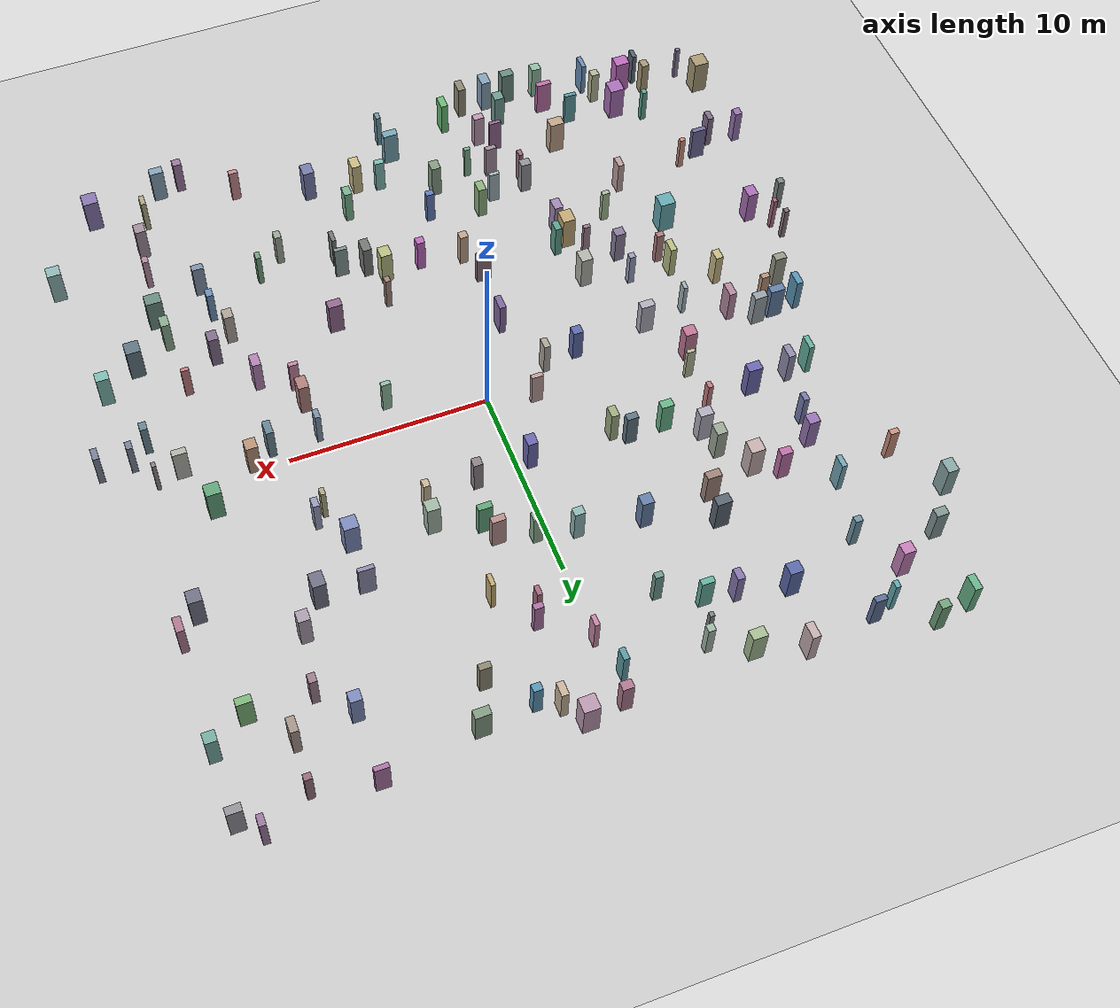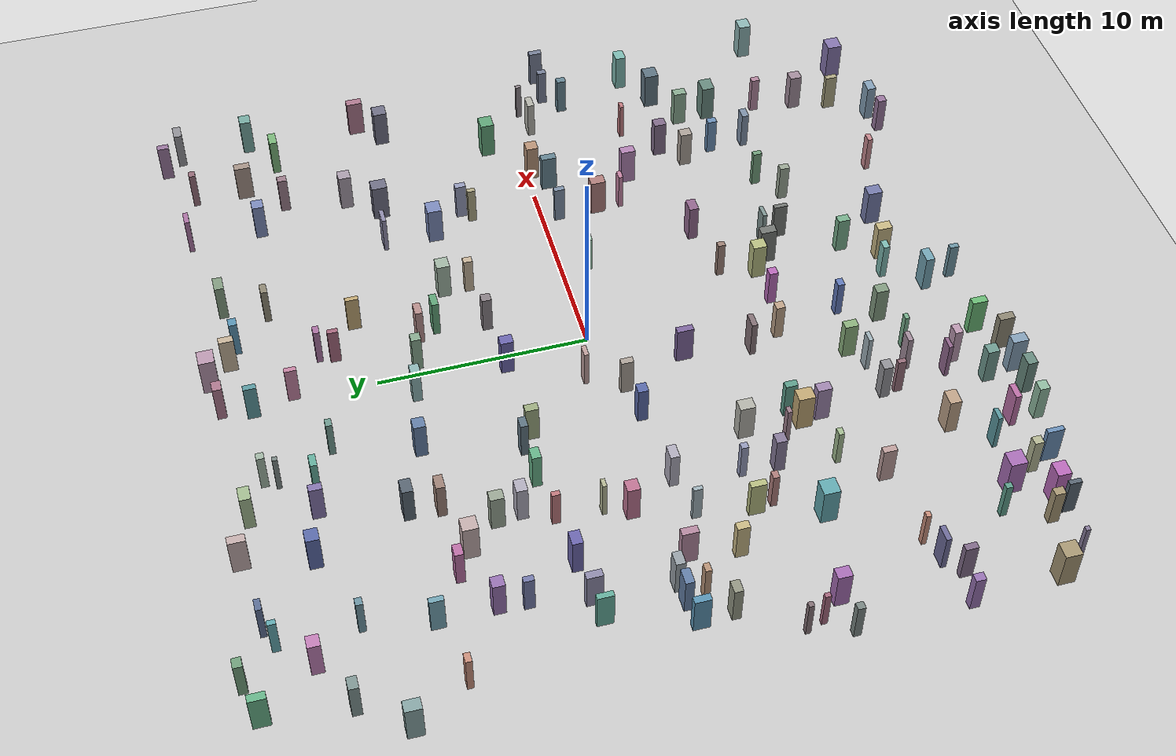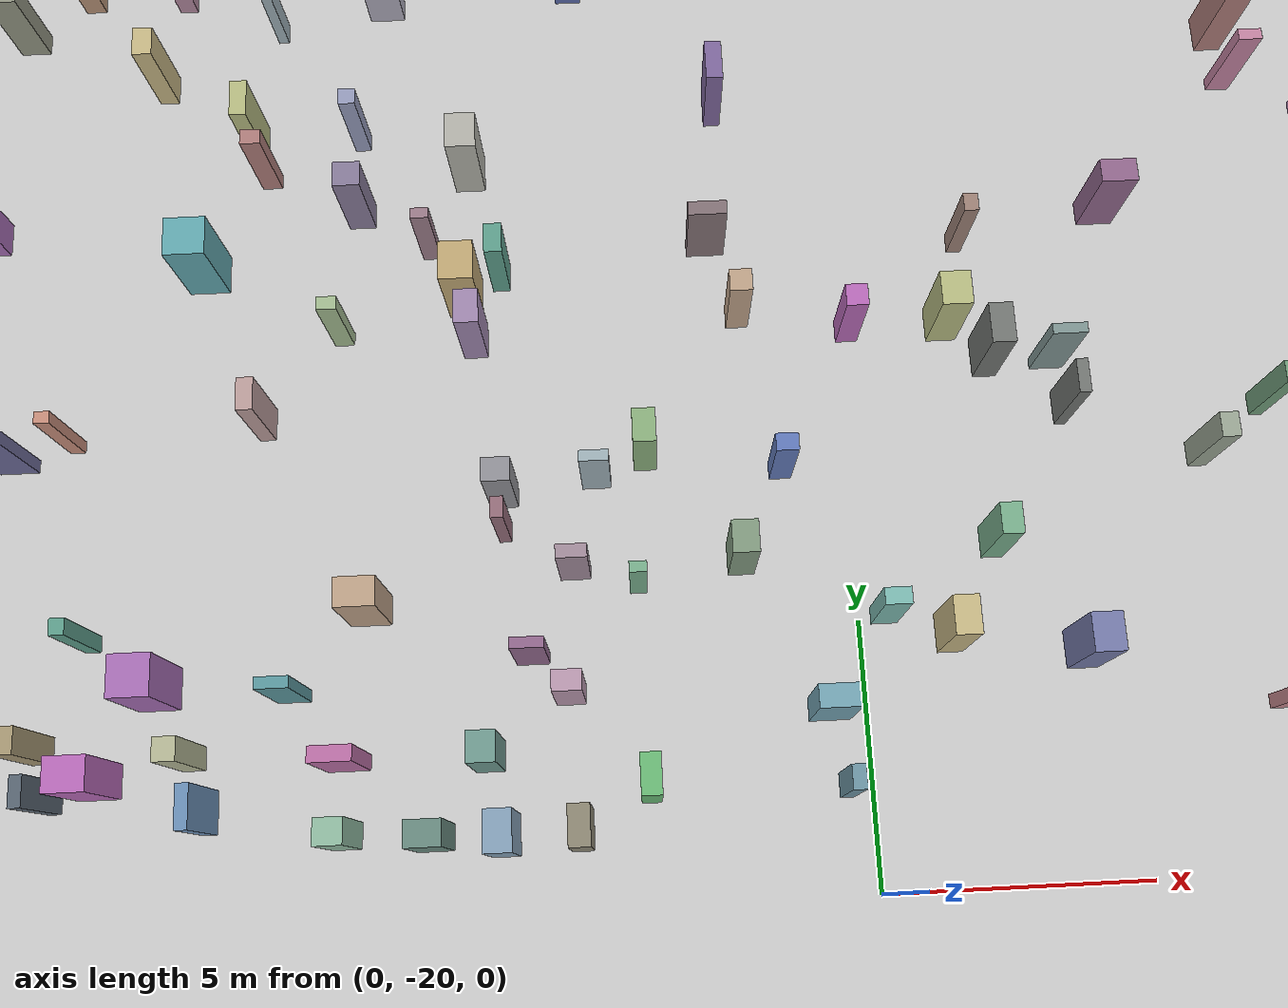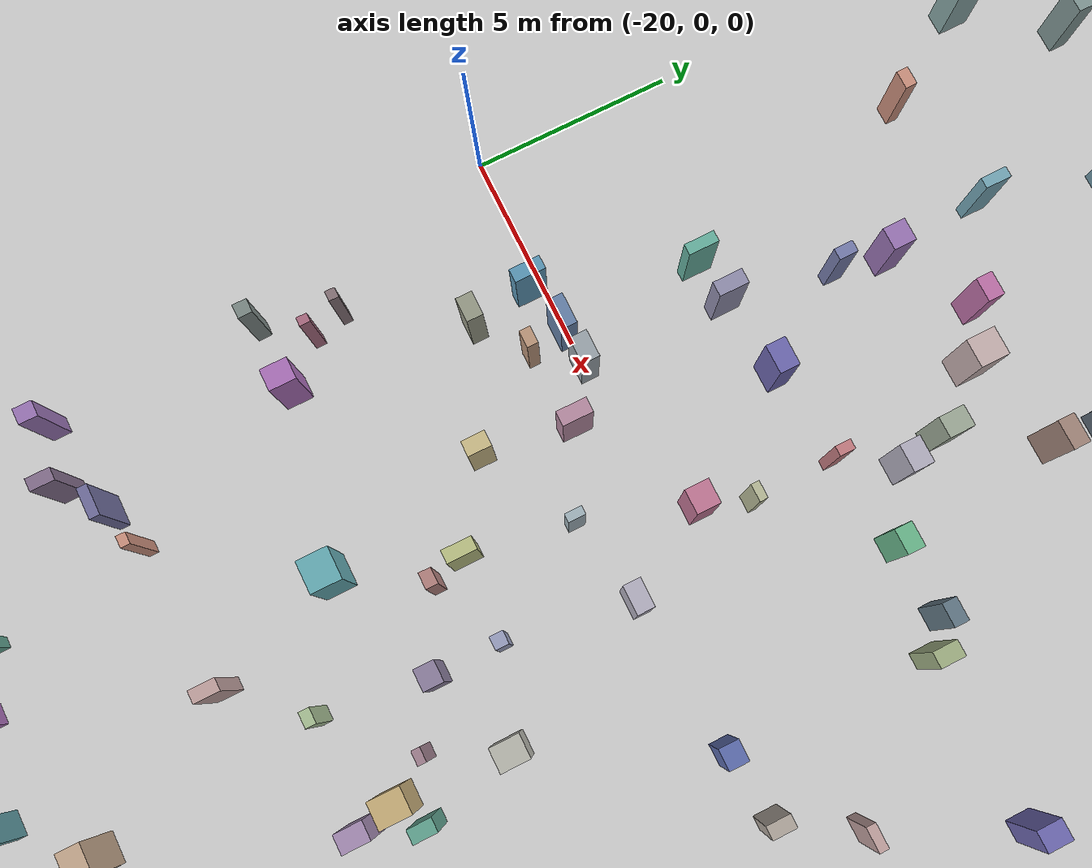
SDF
<?xml version='1.0'?>
<sdf version='1.6'>
  <world name='mockamap_single_floor'>
    <gravity>0 0 -9.8</gravity>
    <include><uri>model://sun</uri></include>
    <include><uri>model://ground_plane</uri></include>
    <gui>
      <camera name='user_camera'>
        <pose>-18 -18 18 0 0.75 0.78</pose>
      </camera>
    </gui>
    <model name='mockamap_box_000'>
      <static>true</static>
      <pose>-15.0321 -17.5841 1.0000 0 0 0</pose>
      <link name='link'>
        <collision name='collision'>
          <geometry><box><size>0.2267 0.5743 2.0000</size></box></geometry>
        </collision>
        <visual name='visual'>
          <geometry><box><size>0.2267 0.5743 2.0000</size></box></geometry>
          <material>
            <ambient>0.350 0.400 0.450 1.000</ambient>
            <diffuse>0.350 0.400 0.450 1.000</diffuse>
          </material>
        </visual>
      </link>
    </model>
    <model name='mockamap_box_001'>
      <static>true</static>
      <pose>6.2818 16.2389 1.0000 0 0 0</pose>
      <link name='link'>
        <collision name='collision'>
          <geometry><box><size>0.7641 0.4449 2.0000</size></box></geometry>
        </collision>
        <visual name='visual'>
          <geometry><box><size>0.7641 0.4449 2.0000</size></box></geometry>
          <material>
            <ambient>0.516 0.613 0.507 1.000</ambient>
            <diffuse>0.516 0.613 0.507 1.000</diffuse>
          </material>
        </visual>
      </link>
    </model>
    <model name='mockamap_box_002'>
      <static>true</static>
      <pose>17.2371 7.7062 1.0000 0 0 0</pose>
      <link name='link'>
        <collision name='collision'>
          <geometry><box><size>0.3860 0.7708 2.0000</size></box></geometry>
        </collision>
        <visual name='visual'>
          <geometry><box><size>0.3860 0.7708 2.0000</size></box></geometry>
          <material>
            <ambient>0.683 0.477 0.564 1.000</ambient>
            <diffuse>0.683 0.477 0.564 1.000</diffuse>
          </material>
        </visual>
      </link>
    </model>
    <model name='mockamap_box_003'>
      <static>true</static>
      <pose>-15.3379 3.4456 1.0000 0 0 0</pose>
      <link name='link'>
        <collision name='collision'>
          <geometry><box><size>0.2746 0.7535 2.0000</size></box></geometry>
        </collision>
        <visual name='visual'>
          <geometry><box><size>0.2746 0.7535 2.0000</size></box></geometry>
          <material>
            <ambient>0.399 0.691 0.621 1.000</ambient>
            <diffuse>0.399 0.691 0.621 1.000</diffuse>
          </material>
        </visual>
      </link>
    </model>
    <model name='mockamap_box_004'>
      <static>true</static>
      <pose>8.7001 7.9001 1.0000 0 0 0</pose>
      <link name='link'>
        <collision name='collision'>
          <geometry><box><size>0.7857 0.2130 2.0000</size></box></geometry>
        </collision>
        <visual name='visual'>
          <geometry><box><size>0.7857 0.2130 2.0000</size></box></geometry>
          <material>
            <ambient>0.566 0.554 0.678 1.000</ambient>
            <diffuse>0.566 0.554 0.678 1.000</diffuse>
          </material>
        </visual>
      </link>
    </model>
    <model name='mockamap_box_005'>
      <static>true</static>
      <pose>0.2145 -9.1443 1.0000 0 0 0</pose>
      <link name='link'>
        <collision name='collision'>
          <geometry><box><size>0.4235 0.4261 2.0000</size></box></geometry>
        </collision>
        <visual name='visual'>
          <geometry><box><size>0.4235 0.4261 2.0000</size></box></geometry>
          <material>
            <ambient>0.732 0.418 0.735 1.000</ambient>
            <diffuse>0.732 0.418 0.735 1.000</diffuse>
          </material>
        </visual>
      </link>
    </model>
    <model name='mockamap_box_006'>
      <static>true</static>
      <pose>8.1564 -11.0577 1.0000 0 0 0</pose>
      <link name='link'>
        <collision name='collision'>
          <geometry><box><size>0.2580 0.4222 2.0000</size></box></geometry>
        </collision>
        <visual name='visual'>
          <geometry><box><size>0.2580 0.4222 2.0000</size></box></geometry>
          <material>
            <ambient>0.449 0.631 0.492 1.000</ambient>
            <diffuse>0.449 0.631 0.492 1.000</diffuse>
          </material>
        </visual>
      </link>
    </model>
    <model name='mockamap_box_007'>
      <static>true</static>
      <pose>12.5498 12.1996 1.0000 0 0 0</pose>
      <link name='link'>
        <collision name='collision'>
          <geometry><box><size>0.3694 0.4579 2.0000</size></box></geometry>
        </collision>
        <visual name='visual'>
          <geometry><box><size>0.3694 0.4579 2.0000</size></box></geometry>
          <material>
            <ambient>0.615 0.494 0.549 1.000</ambient>
            <diffuse>0.615 0.494 0.549 1.000</diffuse>
          </material>
        </visual>
      </link>
    </model>
    <model name='mockamap_box_008'>
      <static>true</static>
      <pose>2.6775 16.4101 1.0000 0 0 0</pose>
      <link name='link'>
        <collision name='collision'>
          <geometry><box><size>0.3515 0.6904 2.0000</size></box></geometry>
        </collision>
        <visual name='visual'>
          <geometry><box><size>0.3515 0.6904 2.0000</size></box></geometry>
          <material>
            <ambient>0.782 0.708 0.606 1.000</ambient>
            <diffuse>0.782 0.708 0.606 1.000</diffuse>
          </material>
        </visual>
      </link>
    </model>
    <model name='mockamap_box_009'>
      <static>true</static>
      <pose>11.1872 -11.3733 1.0000 0 0 0</pose>
      <link name='link'>
        <collision name='collision'>
          <geometry><box><size>0.5878 0.3460 2.0000</size></box></geometry>
        </collision>
        <visual name='visual'>
          <geometry><box><size>0.5878 0.3460 2.0000</size></box></geometry>
          <material>
            <ambient>0.498 0.572 0.663 1.000</ambient>
            <diffuse>0.498 0.572 0.663 1.000</diffuse>
          </material>
        </visual>
      </link>
    </model>
    <model name='mockamap_box_010'>
      <static>true</static>
      <pose>-13.1838 -15.6728 1.0000 0 0 0</pose>
      <link name='link'>
        <collision name='collision'>
          <geometry><box><size>0.7708 0.7841 2.0000</size></box></geometry>
        </collision>
        <visual name='visual'>
          <geometry><box><size>0.7708 0.7841 2.0000</size></box></geometry>
          <material>
            <ambient>0.665 0.435 0.720 1.000</ambient>
            <diffuse>0.665 0.435 0.720 1.000</diffuse>
          </material>
        </visual>
      </link>
    </model>
    <model name='mockamap_box_011'>
      <static>true</static>
      <pose>2.6178 6.7005 1.0000 0 0 0</pose>
      <link name='link'>
        <collision name='collision'>
          <geometry><box><size>0.7099 0.3323 2.0000</size></box></geometry>
        </collision>
        <visual name='visual'>
          <geometry><box><size>0.7099 0.3323 2.0000</size></box></geometry>
          <material>
            <ambient>0.381 0.648 0.477 1.000</ambient>
            <diffuse>0.381 0.648 0.477 1.000</diffuse>
          </material>
        </visual>
      </link>
    </model>
    <model name='mockamap_box_012'>
      <static>true</static>
      <pose>2.1197 4.3284 1.0000 0 0 0</pose>
      <link name='link'>
        <collision name='collision'>
          <geometry><box><size>0.4533 0.4592 2.0000</size></box></geometry>
        </collision>
        <visual name='visual'>
          <geometry><box><size>0.4533 0.4592 2.0000</size></box></geometry>
          <material>
            <ambient>0.548 0.512 0.534 1.000</ambient>
            <diffuse>0.548 0.512 0.534 1.000</diffuse>
          </material>
        </visual>
      </link>
    </model>
    <model name='mockamap_box_013'>
      <static>true</static>
      <pose>-9.7718 1.9524 1.0000 0 0 0</pose>
      <link name='link'>
        <collision name='collision'>
          <geometry><box><size>0.4269 0.2035 2.0000</size></box></geometry>
        </collision>
        <visual name='visual'>
          <geometry><box><size>0.4269 0.2035 2.0000</size></box></geometry>
          <material>
            <ambient>0.715 0.726 0.591 1.000</ambient>
            <diffuse>0.715 0.726 0.591 1.000</diffuse>
          </material>
        </visual>
      </link>
    </model>
    <model name='mockamap_box_014'>
      <static>true</static>
      <pose>-12.9841 13.2362 1.0000 0 0 0</pose>
      <link name='link'>
        <collision name='collision'>
          <geometry><box><size>0.3698 0.3169 2.0000</size></box></geometry>
        </collision>
        <visual name='visual'>
          <geometry><box><size>0.3698 0.3169 2.0000</size></box></geometry>
          <material>
            <ambient>0.431 0.589 0.648 1.000</ambient>
            <diffuse>0.431 0.589 0.648 1.000</diffuse>
          </material>
        </visual>
      </link>
    </model>
    <model name='mockamap_box_015'>
      <static>true</static>
      <pose>-13.5221 7.5409 1.0000 0 0 0</pose>
      <link name='link'>
        <collision name='collision'>
          <geometry><box><size>0.5592 0.5615 2.0000</size></box></geometry>
        </collision>
        <visual name='visual'>
          <geometry><box><size>0.5592 0.5615 2.0000</size></box></geometry>
          <material>
            <ambient>0.597 0.453 0.705 1.000</ambient>
            <diffuse>0.597 0.453 0.705 1.000</diffuse>
          </material>
        </visual>
      </link>
    </model>
    <model name='mockamap_box_016'>
      <static>true</static>
      <pose>-7.3450 -8.0702 1.0000 0 0 0</pose>
      <link name='link'>
        <collision name='collision'>
          <geometry><box><size>0.6593 0.7731 2.0000</size></box></geometry>
        </collision>
        <visual name='visual'>
          <geometry><box><size>0.6593 0.7731 2.0000</size></box></geometry>
          <material>
            <ambient>0.764 0.666 0.462 1.000</ambient>
            <diffuse>0.764 0.666 0.462 1.000</diffuse>
          </material>
        </visual>
      </link>
    </model>
    <model name='mockamap_box_017'>
      <static>true</static>
      <pose>-18.5719 -6.4431 1.0000 0 0 0</pose>
      <link name='link'>
        <collision name='collision'>
          <geometry><box><size>0.3442 0.3489 2.0000</size></box></geometry>
        </collision>
        <visual name='visual'>
          <geometry><box><size>0.3442 0.3489 2.0000</size></box></geometry>
          <material>
            <ambient>0.480 0.530 0.519 1.000</ambient>
            <diffuse>0.480 0.530 0.519 1.000</diffuse>
          </material>
        </visual>
      </link>
    </model>
    <model name='mockamap_box_018'>
      <static>true</static>
      <pose>-6.2782 16.9180 1.0000 0 0 0</pose>
      <link name='link'>
        <collision name='collision'>
          <geometry><box><size>0.7214 0.5166 2.0000</size></box></geometry>
        </collision>
        <visual name='visual'>
          <geometry><box><size>0.7214 0.5166 2.0000</size></box></geometry>
          <material>
            <ambient>0.647 0.743 0.576 1.000</ambient>
            <diffuse>0.647 0.743 0.576 1.000</diffuse>
          </material>
        </visual>
      </link>
    </model>
    <model name='mockamap_box_019'>
      <static>true</static>
      <pose>-10.6722 -15.9207 1.0000 0 0 0</pose>
      <link name='link'>
        <collision name='collision'>
          <geometry><box><size>0.6190 0.2158 2.0000</size></box></geometry>
        </collision>
        <visual name='visual'>
          <geometry><box><size>0.6190 0.2158 2.0000</size></box></geometry>
          <material>
            <ambient>0.363 0.607 0.633 1.000</ambient>
            <diffuse>0.363 0.607 0.633 1.000</diffuse>
          </material>
        </visual>
      </link>
    </model>
    <model name='mockamap_box_020'>
      <static>true</static>
      <pose>15.1869 -17.6498 1.0000 0 0 0</pose>
      <link name='link'>
        <collision name='collision'>
          <geometry><box><size>0.7612 0.7426 2.0000</size></box></geometry>
        </collision>
        <visual name='visual'>
          <geometry><box><size>0.7612 0.7426 2.0000</size></box></geometry>
          <material>
            <ambient>0.530 0.470 0.690 1.000</ambient>
            <diffuse>0.530 0.470 0.690 1.000</diffuse>
          </material>
        </visual>
      </link>
    </model>
    <model name='mockamap_box_021'>
      <static>true</static>
      <pose>-8.9207 -1.4252 1.0000 0 0 0</pose>
      <link name='link'>
        <collision name='collision'>
          <geometry><box><size>0.7100 0.4261 2.0000</size></box></geometry>
        </collision>
        <visual name='visual'>
          <geometry><box><size>0.7100 0.4261 2.0000</size></box></geometry>
          <material>
            <ambient>0.696 0.683 0.747 1.000</ambient>
            <diffuse>0.696 0.683 0.747 1.000</diffuse>
          </material>
        </visual>
      </link>
    </model>
    <model name='mockamap_box_022'>
      <static>true</static>
      <pose>-8.0454 -18.6199 1.0000 0 0 0</pose>
      <link name='link'>
        <collision name='collision'>
          <geometry><box><size>0.6732 0.4795 2.0000</size></box></geometry>
        </collision>
        <visual name='visual'>
          <geometry><box><size>0.6732 0.4795 2.0000</size></box></geometry>
          <material>
            <ambient>0.413 0.547 0.504 1.000</ambient>
            <diffuse>0.413 0.547 0.504 1.000</diffuse>
          </material>
        </visual>
      </link>
    </model>
    <model name='mockamap_box_023'>
      <static>true</static>
      <pose>5.4816 -6.8172 1.0000 0 0 0</pose>
      <link name='link'>
        <collision name='collision'>
          <geometry><box><size>0.7093 0.4625 2.0000</size></box></geometry>
        </collision>
        <visual name='visual'>
          <geometry><box><size>0.7093 0.4625 2.0000</size></box></geometry>
          <material>
            <ambient>0.579 0.411 0.561 1.000</ambient>
            <diffuse>0.579 0.411 0.561 1.000</diffuse>
          </material>
        </visual>
      </link>
    </model>
    <model name='mockamap_box_024'>
      <static>true</static>
      <pose>-11.2739 -10.5561 1.0000 0 0 0</pose>
      <link name='link'>
        <collision name='collision'>
          <geometry><box><size>0.3173 0.6329 2.0000</size></box></geometry>
        </collision>
        <visual name='visual'>
          <geometry><box><size>0.3173 0.6329 2.0000</size></box></geometry>
          <material>
            <ambient>0.746 0.624 0.618 1.000</ambient>
            <diffuse>0.746 0.624 0.618 1.000</diffuse>
          </material>
        </visual>
      </link>
    </model>
    <model name='mockamap_box_025'>
      <static>true</static>
      <pose>-13.7292 6.2781 1.0000 0 0 0</pose>
      <link name='link'>
        <collision name='collision'>
          <geometry><box><size>0.2813 0.4722 2.0000</size></box></geometry>
        </collision>
        <visual name='visual'>
          <geometry><box><size>0.2813 0.4722 2.0000</size></box></geometry>
          <material>
            <ambient>0.462 0.488 0.675 1.000</ambient>
            <diffuse>0.462 0.488 0.675 1.000</diffuse>
          </material>
        </visual>
      </link>
    </model>
    <model name='mockamap_box_026'>
      <static>true</static>
      <pose>-11.1184 -1.8605 1.0000 0 0 0</pose>
      <link name='link'>
        <collision name='collision'>
          <geometry><box><size>0.2078 0.4240 2.0000</size></box></geometry>
        </collision>
        <visual name='visual'>
          <geometry><box><size>0.2078 0.4240 2.0000</size></box></geometry>
          <material>
            <ambient>0.629 0.701 0.732 1.000</ambient>
            <diffuse>0.629 0.701 0.732 1.000</diffuse>
          </material>
        </visual>
      </link>
    </model>
    <model name='mockamap_box_027'>
      <static>true</static>
      <pose>-14.9859 -10.8422 1.0000 0 0 0</pose>
      <link name='link'>
        <collision name='collision'>
          <geometry><box><size>0.2858 0.2299 2.0000</size></box></geometry>
        </collision>
        <visual name='visual'>
          <geometry><box><size>0.2858 0.2299 2.0000</size></box></geometry>
          <material>
            <ambient>0.796 0.565 0.489 1.000</ambient>
            <diffuse>0.796 0.565 0.489 1.000</diffuse>
          </material>
        </visual>
      </link>
    </model>
    <model name='mockamap_box_028'>
      <static>true</static>
      <pose>-17.0172 -11.9449 1.0000 0 0 0</pose>
      <link name='link'>
        <collision name='collision'>
          <geometry><box><size>0.3143 0.5909 2.0000</size></box></geometry>
        </collision>
        <visual name='visual'>
          <geometry><box><size>0.3143 0.5909 2.0000</size></box></geometry>
          <material>
            <ambient>0.512 0.428 0.546 1.000</ambient>
            <diffuse>0.512 0.428 0.546 1.000</diffuse>
          </material>
        </visual>
      </link>
    </model>
    <model name='mockamap_box_029'>
      <static>true</static>
      <pose>10.5710 -8.0434 1.0000 0 0 0</pose>
      <link name='link'>
        <collision name='collision'>
          <geometry><box><size>0.4899 0.5765 2.0000</size></box></geometry>
        </collision>
        <visual name='visual'>
          <geometry><box><size>0.4899 0.5765 2.0000</size></box></geometry>
          <material>
            <ambient>0.678 0.641 0.603 1.000</ambient>
            <diffuse>0.678 0.641 0.603 1.000</diffuse>
          </material>
        </visual>
      </link>
    </model>
    <model name='mockamap_box_030'>
      <static>true</static>
      <pose>-15.3202 -0.0906 1.0000 0 0 0</pose>
      <link name='link'>
        <collision name='collision'>
          <geometry><box><size>0.7618 0.4082 2.0000</size></box></geometry>
        </collision>
        <visual name='visual'>
          <geometry><box><size>0.7618 0.4082 2.0000</size></box></geometry>
          <material>
            <ambient>0.395 0.505 0.660 1.000</ambient>
            <diffuse>0.395 0.505 0.660 1.000</diffuse>
          </material>
        </visual>
      </link>
    </model>
    <model name='mockamap_box_031'>
      <static>true</static>
      <pose>17.9842 -13.6035 1.0000 0 0 0</pose>
      <link name='link'>
        <collision name='collision'>
          <geometry><box><size>0.6874 0.6146 2.0000</size></box></geometry>
        </collision>
        <visual name='visual'>
          <geometry><box><size>0.6874 0.6146 2.0000</size></box></geometry>
          <material>
            <ambient>0.561 0.719 0.717 1.000</ambient>
            <diffuse>0.561 0.719 0.717 1.000</diffuse>
          </material>
        </visual>
      </link>
    </model>
    <model name='mockamap_box_032'>
      <static>true</static>
      <pose>-15.1227 -1.0097 1.0000 0 0 0</pose>
      <link name='link'>
        <collision name='collision'>
          <geometry><box><size>0.4203 0.2797 2.0000</size></box></geometry>
        </collision>
        <visual name='visual'>
          <geometry><box><size>0.4203 0.2797 2.0000</size></box></geometry>
          <material>
            <ambient>0.728 0.582 0.474 1.000</ambient>
            <diffuse>0.728 0.582 0.474 1.000</diffuse>
          </material>
        </visual>
      </link>
    </model>
    <model name='mockamap_box_033'>
      <static>true</static>
      <pose>10.9038 7.6736 1.0000 0 0 0</pose>
      <link name='link'>
        <collision name='collision'>
          <geometry><box><size>0.6380 0.7614 2.0000</size></box></geometry>
        </collision>
        <visual name='visual'>
          <geometry><box><size>0.6380 0.7614 2.0000</size></box></geometry>
          <material>
            <ambient>0.445 0.446 0.531 1.000</ambient>
            <diffuse>0.445 0.446 0.531 1.000</diffuse>
          </material>
        </visual>
      </link>
    </model>
    <model name='mockamap_box_034'>
      <static>true</static>
      <pose>-9.1957 6.5623 1.0000 0 0 0</pose>
      <link name='link'>
        <collision name='collision'>
          <geometry><box><size>0.5228 0.6341 2.0000</size></box></geometry>
        </collision>
        <visual name='visual'>
          <geometry><box><size>0.5228 0.6341 2.0000</size></box></geometry>
          <material>
            <ambient>0.611 0.659 0.588 1.000</ambient>
            <diffuse>0.611 0.659 0.588 1.000</diffuse>
          </material>
        </visual>
      </link>
    </model>
    <model name='mockamap_box_035'>
      <static>true</static>
      <pose>8.4592 -3.9993 1.0000 0 0 0</pose>
      <link name='link'>
        <collision name='collision'>
          <geometry><box><size>0.4658 0.2275 2.0000</size></box></geometry>
        </collision>
        <visual name='visual'>
          <geometry><box><size>0.4658 0.2275 2.0000</size></box></geometry>
          <material>
            <ambient>0.777 0.522 0.645 1.000</ambient>
            <diffuse>0.777 0.522 0.645 1.000</diffuse>
          </material>
        </visual>
      </link>
    </model>
    <model name='mockamap_box_036'>
      <static>true</static>
      <pose>0.4680 -14.9104 1.0000 0 0 0</pose>
      <link name='link'>
        <collision name='collision'>
          <geometry><box><size>0.4964 0.3110 2.0000</size></box></geometry>
        </collision>
        <visual name='visual'>
          <geometry><box><size>0.4964 0.3110 2.0000</size></box></geometry>
          <material>
            <ambient>0.494 0.736 0.702 1.000</ambient>
            <diffuse>0.494 0.736 0.702 1.000</diffuse>
          </material>
        </visual>
      </link>
    </model>
    <model name='mockamap_box_037'>
      <static>true</static>
      <pose>-18.2314 -15.8954 1.0000 0 0 0</pose>
      <link name='link'>
        <collision name='collision'>
          <geometry><box><size>0.7818 0.7815 2.0000</size></box></geometry>
        </collision>
        <visual name='visual'>
          <geometry><box><size>0.7818 0.7815 2.0000</size></box></geometry>
          <material>
            <ambient>0.660 0.600 0.459 1.000</ambient>
            <diffuse>0.660 0.600 0.459 1.000</diffuse>
          </material>
        </visual>
      </link>
    </model>
    <model name='mockamap_box_038'>
      <static>true</static>
      <pose>-5.5987 4.4739 1.0000 0 0 0</pose>
      <link name='link'>
        <collision name='collision'>
          <geometry><box><size>0.5717 0.3587 2.0000</size></box></geometry>
        </collision>
        <visual name='visual'>
          <geometry><box><size>0.5717 0.3587 2.0000</size></box></geometry>
          <material>
            <ambient>0.377 0.463 0.516 1.000</ambient>
            <diffuse>0.377 0.463 0.516 1.000</diffuse>
          </material>
        </visual>
      </link>
    </model>
    <model name='mockamap_box_039'>
      <static>true</static>
      <pose>13.5970 -8.6630 1.0000 0 0 0</pose>
      <link name='link'>
        <collision name='collision'>
          <geometry><box><size>0.4249 0.6387 2.0000</size></box></geometry>
        </collision>
        <visual name='visual'>
          <geometry><box><size>0.4249 0.6387 2.0000</size></box></geometry>
          <material>
            <ambient>0.543 0.676 0.573 1.000</ambient>
            <diffuse>0.543 0.676 0.573 1.000</diffuse>
          </material>
        </visual>
      </link>
    </model>
    <model name='mockamap_box_040'>
      <static>true</static>
      <pose>13.5120 -12.7550 1.0000 0 0 0</pose>
      <link name='link'>
        <collision name='collision'>
          <geometry><box><size>0.3060 0.4020 2.0000</size></box></geometry>
        </collision>
        <visual name='visual'>
          <geometry><box><size>0.3060 0.4020 2.0000</size></box></geometry>
          <material>
            <ambient>0.710 0.540 0.630 1.000</ambient>
            <diffuse>0.710 0.540 0.630 1.000</diffuse>
          </material>
        </visual>
      </link>
    </model>
    <model name='mockamap_box_041'>
      <static>true</static>
      <pose>-0.6810 4.0384 1.0000 0 0 0</pose>
      <link name='link'>
        <collision name='collision'>
          <geometry><box><size>0.5067 0.6144 2.0000</size></box></geometry>
        </collision>
        <visual name='visual'>
          <geometry><box><size>0.5067 0.6144 2.0000</size></box></geometry>
          <material>
            <ambient>0.426 0.404 0.687 1.000</ambient>
            <diffuse>0.426 0.404 0.687 1.000</diffuse>
          </material>
        </visual>
      </link>
    </model>
    <model name='mockamap_box_042'>
      <static>true</static>
      <pose>-9.4270 -4.5137 1.0000 0 0 0</pose>
      <link name='link'>
        <collision name='collision'>
          <geometry><box><size>0.3187 0.3254 2.0000</size></box></geometry>
        </collision>
        <visual name='visual'>
          <geometry><box><size>0.3187 0.3254 2.0000</size></box></geometry>
          <material>
            <ambient>0.593 0.617 0.744 1.000</ambient>
            <diffuse>0.593 0.617 0.744 1.000</diffuse>
          </material>
        </visual>
      </link>
    </model>
    <model name='mockamap_box_043'>
      <static>true</static>
      <pose>-9.7795 4.0861 1.0000 0 0 0</pose>
      <link name='link'>
        <collision name='collision'>
          <geometry><box><size>0.2436 0.3837 2.0000</size></box></geometry>
        </collision>
        <visual name='visual'>
          <geometry><box><size>0.2436 0.3837 2.0000</size></box></geometry>
          <material>
            <ambient>0.760 0.481 0.501 1.000</ambient>
            <diffuse>0.760 0.481 0.501 1.000</diffuse>
          </material>
        </visual>
      </link>
    </model>
    <model name='mockamap_box_044'>
      <static>true</static>
      <pose>2.6485 -13.5885 1.0000 0 0 0</pose>
      <link name='link'>
        <collision name='collision'>
          <geometry><box><size>0.4067 0.5897 2.0000</size></box></geometry>
        </collision>
        <visual name='visual'>
          <geometry><box><size>0.4067 0.5897 2.0000</size></box></geometry>
          <material>
            <ambient>0.476 0.694 0.558 1.000</ambient>
            <diffuse>0.476 0.694 0.558 1.000</diffuse>
          </material>
        </visual>
      </link>
    </model>
    <model name='mockamap_box_045'>
      <static>true</static>
      <pose>13.2676 -14.8459 1.0000 0 0 0</pose>
      <link name='link'>
        <collision name='collision'>
          <geometry><box><size>0.5390 0.5967 2.0000</size></box></geometry>
        </collision>
        <visual name='visual'>
          <geometry><box><size>0.5390 0.5967 2.0000</size></box></geometry>
          <material>
            <ambient>0.642 0.557 0.615 1.000</ambient>
            <diffuse>0.642 0.557 0.615 1.000</diffuse>
          </material>
        </visual>
      </link>
    </model>
    <model name='mockamap_box_046'>
      <static>true</static>
      <pose>-9.1847 14.5162 1.0000 0 0 0</pose>
      <link name='link'>
        <collision name='collision'>
          <geometry><box><size>0.6496 0.6085 2.0000</size></box></geometry>
        </collision>
        <visual name='visual'>
          <geometry><box><size>0.6496 0.6085 2.0000</size></box></geometry>
          <material>
            <ambient>0.359 0.421 0.672 1.000</ambient>
            <diffuse>0.359 0.421 0.672 1.000</diffuse>
          </material>
        </visual>
      </link>
    </model>
    <model name='mockamap_box_047'>
      <static>true</static>
      <pose>11.5087 -18.3367 1.0000 0 0 0</pose>
      <link name='link'>
        <collision name='collision'>
          <geometry><box><size>0.6854 0.4426 2.0000</size></box></geometry>
        </collision>
        <visual name='visual'>
          <geometry><box><size>0.6854 0.4426 2.0000</size></box></geometry>
          <material>
            <ambient>0.525 0.635 0.729 1.000</ambient>
            <diffuse>0.525 0.635 0.729 1.000</diffuse>
          </material>
        </visual>
      </link>
    </model>
    <model name='mockamap_box_048'>
      <static>true</static>
      <pose>8.3840 -2.8104 1.0000 0 0 0</pose>
      <link name='link'>
        <collision name='collision'>
          <geometry><box><size>0.5285 0.7263 2.0000</size></box></geometry>
        </collision>
        <visual name='visual'>
          <geometry><box><size>0.5285 0.7263 2.0000</size></box></geometry>
          <material>
            <ambient>0.692 0.498 0.486 1.000</ambient>
            <diffuse>0.692 0.498 0.486 1.000</diffuse>
          </material>
        </visual>
      </link>
    </model>
    <model name='mockamap_box_049'>
      <static>true</static>
      <pose>-7.4207 4.3815 1.0000 0 0 0</pose>
      <link name='link'>
        <collision name='collision'>
          <geometry><box><size>0.6167 0.4328 2.0000</size></box></geometry>
        </collision>
        <visual name='visual'>
          <geometry><box><size>0.6167 0.4328 2.0000</size></box></geometry>
          <material>
            <ambient>0.408 0.712 0.543 1.000</ambient>
            <diffuse>0.408 0.712 0.543 1.000</diffuse>
          </material>
        </visual>
      </link>
    </model>
    <model name='mockamap_box_050'>
      <static>true</static>
      <pose>17.3284 16.7434 1.0000 0 0 0</pose>
      <link name='link'>
        <collision name='collision'>
          <geometry><box><size>0.7277 0.3998 2.0000</size></box></geometry>
        </collision>
        <visual name='visual'>
          <geometry><box><size>0.7277 0.3998 2.0000</size></box></geometry>
          <material>
            <ambient>0.575 0.575 0.600 1.000</ambient>
            <diffuse>0.575 0.575 0.600 1.000</diffuse>
          </material>
        </visual>
      </link>
    </model>
    <model name='mockamap_box_051'>
      <static>true</static>
      <pose>-9.6437 -17.1984 1.0000 0 0 0</pose>
      <link name='link'>
        <collision name='collision'>
          <geometry><box><size>0.7874 0.2933 2.0000</size></box></geometry>
        </collision>
        <visual name='visual'>
          <geometry><box><size>0.7874 0.2933 2.0000</size></box></geometry>
          <material>
            <ambient>0.741 0.439 0.657 1.000</ambient>
            <diffuse>0.741 0.439 0.657 1.000</diffuse>
          </material>
        </visual>
      </link>
    </model>
    <model name='mockamap_box_052'>
      <static>true</static>
      <pose>-13.7165 10.1662 1.0000 0 0 0</pose>
      <link name='link'>
        <collision name='collision'>
          <geometry><box><size>0.2646 0.6470 2.0000</size></box></geometry>
        </collision>
        <visual name='visual'>
          <geometry><box><size>0.2646 0.6470 2.0000</size></box></geometry>
          <material>
            <ambient>0.458 0.652 0.714 1.000</ambient>
            <diffuse>0.458 0.652 0.714 1.000</diffuse>
          </material>
        </visual>
      </link>
    </model>
    <model name='mockamap_box_053'>
      <static>true</static>
      <pose>2.5545 -7.3487 1.0000 0 0 0</pose>
      <link name='link'>
        <collision name='collision'>
          <geometry><box><size>0.2836 0.3546 2.0000</size></box></geometry>
        </collision>
        <visual name='visual'>
          <geometry><box><size>0.2836 0.3546 2.0000</size></box></geometry>
          <material>
            <ambient>0.624 0.516 0.471 1.000</ambient>
            <diffuse>0.624 0.516 0.471 1.000</diffuse>
          </material>
        </visual>
      </link>
    </model>
    <model name='mockamap_box_054'>
      <static>true</static>
      <pose>1.6635 -15.3077 1.0000 0 0 0</pose>
      <link name='link'>
        <collision name='collision'>
          <geometry><box><size>0.4880 0.7212 2.0000</size></box></geometry>
        </collision>
        <visual name='visual'>
          <geometry><box><size>0.4880 0.7212 2.0000</size></box></geometry>
          <material>
            <ambient>0.791 0.729 0.528 1.000</ambient>
            <diffuse>0.791 0.729 0.528 1.000</diffuse>
          </material>
        </visual>
      </link>
    </model>
    <model name='mockamap_box_055'>
      <static>true</static>
      <pose>-16.6939 14.1934 1.0000 0 0 0</pose>
      <link name='link'>
        <collision name='collision'>
          <geometry><box><size>0.6025 0.4378 2.0000</size></box></geometry>
        </collision>
        <visual name='visual'>
          <geometry><box><size>0.6025 0.4378 2.0000</size></box></geometry>
          <material>
            <ambient>0.507 0.593 0.585 1.000</ambient>
            <diffuse>0.507 0.593 0.585 1.000</diffuse>
          </material>
        </visual>
      </link>
    </model>
    <model name='mockamap_box_056'>
      <static>true</static>
      <pose>11.0569 17.1082 1.0000 0 0 0</pose>
      <link name='link'>
        <collision name='collision'>
          <geometry><box><size>0.6971 0.2421 2.0000</size></box></geometry>
        </collision>
        <visual name='visual'>
          <geometry><box><size>0.6971 0.2421 2.0000</size></box></geometry>
          <material>
            <ambient>0.674 0.456 0.642 1.000</ambient>
            <diffuse>0.674 0.456 0.642 1.000</diffuse>
          </material>
        </visual>
      </link>
    </model>
    <model name='mockamap_box_057'>
      <static>true</static>
      <pose>-13.0534 16.8394 1.0000 0 0 0</pose>
      <link name='link'>
        <collision name='collision'>
          <geometry><box><size>0.2445 0.3728 2.0000</size></box></geometry>
        </collision>
        <visual name='visual'>
          <geometry><box><size>0.2445 0.3728 2.0000</size></box></geometry>
          <material>
            <ambient>0.390 0.669 0.699 1.000</ambient>
            <diffuse>0.390 0.669 0.699 1.000</diffuse>
          </material>
        </visual>
      </link>
    </model>
    <model name='mockamap_box_058'>
      <static>true</static>
      <pose>-5.3612 -18.6135 1.0000 0 0 0</pose>
      <link name='link'>
        <collision name='collision'>
          <geometry><box><size>0.3967 0.7427 2.0000</size></box></geometry>
        </collision>
        <visual name='visual'>
          <geometry><box><size>0.3967 0.7427 2.0000</size></box></geometry>
          <material>
            <ambient>0.557 0.533 0.456 1.000</ambient>
            <diffuse>0.557 0.533 0.456 1.000</diffuse>
          </material>
        </visual>
      </link>
    </model>
    <model name='mockamap_box_059'>
      <static>true</static>
      <pose>2.1037 -9.0892 1.0000 0 0 0</pose>
      <link name='link'>
        <collision name='collision'>
          <geometry><box><size>0.5887 0.6668 2.0000</size></box></geometry>
        </collision>
        <visual name='visual'>
          <geometry><box><size>0.5887 0.6668 2.0000</size></box></geometry>
          <material>
            <ambient>0.724 0.746 0.513 1.000</ambient>
            <diffuse>0.724 0.746 0.513 1.000</diffuse>
          </material>
        </visual>
      </link>
    </model>
    <model name='mockamap_box_060'>
      <static>true</static>
      <pose>-3.3759 12.7470 1.0000 0 0 0</pose>
      <link name='link'>
        <collision name='collision'>
          <geometry><box><size>0.4164 0.2947 2.0000</size></box></geometry>
        </collision>
        <visual name='visual'>
          <geometry><box><size>0.4164 0.2947 2.0000</size></box></geometry>
          <material>
            <ambient>0.440 0.610 0.570 1.000</ambient>
            <diffuse>0.440 0.610 0.570 1.000</diffuse>
          </material>
        </visual>
      </link>
    </model>
    <model name='mockamap_box_061'>
      <static>true</static>
      <pose>16.3893 17.5754 1.0000 0 0 0</pose>
      <link name='link'>
        <collision name='collision'>
          <geometry><box><size>0.3185 0.5636 2.0000</size></box></geometry>
        </collision>
        <visual name='visual'>
          <geometry><box><size>0.3185 0.5636 2.0000</size></box></geometry>
          <material>
            <ambient>0.607 0.474 0.627 1.000</ambient>
            <diffuse>0.607 0.474 0.627 1.000</diffuse>
          </material>
        </visual>
      </link>
    </model>
    <model name='mockamap_box_062'>
      <static>true</static>
      <pose>-8.5721 17.6052 1.0000 0 0 0</pose>
      <link name='link'>
        <collision name='collision'>
          <geometry><box><size>0.3972 0.7924 2.0000</size></box></geometry>
        </collision>
        <visual name='visual'>
          <geometry><box><size>0.3972 0.7924 2.0000</size></box></geometry>
          <material>
            <ambient>0.773 0.687 0.684 1.000</ambient>
            <diffuse>0.773 0.687 0.684 1.000</diffuse>
          </material>
        </visual>
      </link>
    </model>
    <model name='mockamap_box_063'>
      <static>true</static>
      <pose>8.6541 5.4035 1.0000 0 0 0</pose>
      <link name='link'>
        <collision name='collision'>
          <geometry><box><size>0.7348 0.7013 2.0000</size></box></geometry>
        </collision>
        <visual name='visual'>
          <geometry><box><size>0.7348 0.7013 2.0000</size></box></geometry>
          <material>
            <ambient>0.489 0.550 0.741 1.000</ambient>
            <diffuse>0.489 0.550 0.741 1.000</diffuse>
          </material>
        </visual>
      </link>
    </model>
    <model name='mockamap_box_064'>
      <static>true</static>
      <pose>1.9212 11.6076 1.0000 0 0 0</pose>
      <link name='link'>
        <collision name='collision'>
          <geometry><box><size>0.2420 0.5027 2.0000</size></box></geometry>
        </collision>
        <visual name='visual'>
          <geometry><box><size>0.2420 0.5027 2.0000</size></box></geometry>
          <material>
            <ambient>0.656 0.414 0.498 1.000</ambient>
            <diffuse>0.656 0.414 0.498 1.000</diffuse>
          </material>
        </visual>
      </link>
    </model>
    <model name='mockamap_box_065'>
      <static>true</static>
      <pose>-6.6294 -7.6510 1.0000 0 0 0</pose>
      <link name='link'>
        <collision name='collision'>
          <geometry><box><size>0.3435 0.5827 2.0000</size></box></geometry>
        </collision>
        <visual name='visual'>
          <geometry><box><size>0.3435 0.5827 2.0000</size></box></geometry>
          <material>
            <ambient>0.372 0.628 0.555 1.000</ambient>
            <diffuse>0.372 0.628 0.555 1.000</diffuse>
          </material>
        </visual>
      </link>
    </model>
    <model name='mockamap_box_066'>
      <static>true</static>
      <pose>-9.4309 -6.1793 1.0000 0 0 0</pose>
      <link name='link'>
        <collision name='collision'>
          <geometry><box><size>0.5277 0.4964 2.0000</size></box></geometry>
        </collision>
        <visual name='visual'>
          <geometry><box><size>0.5277 0.4964 2.0000</size></box></geometry>
          <material>
            <ambient>0.539 0.491 0.612 1.000</ambient>
            <diffuse>0.539 0.491 0.612 1.000</diffuse>
          </material>
        </visual>
      </link>
    </model>
    <model name='mockamap_box_067'>
      <static>true</static>
      <pose>14.8944 -1.0081 1.0000 0 0 0</pose>
      <link name='link'>
        <collision name='collision'>
          <geometry><box><size>0.7002 0.3442 2.0000</size></box></geometry>
        </collision>
        <visual name='visual'>
          <geometry><box><size>0.7002 0.3442 2.0000</size></box></geometry>
          <material>
            <ambient>0.706 0.705 0.669 1.000</ambient>
            <diffuse>0.706 0.705 0.669 1.000</diffuse>
          </material>
        </visual>
      </link>
    </model>
    <model name='mockamap_box_068'>
      <static>true</static>
      <pose>11.0686 -9.6048 1.0000 0 0 0</pose>
      <link name='link'>
        <collision name='collision'>
          <geometry><box><size>0.3391 0.4649 2.0000</size></box></geometry>
        </collision>
        <visual name='visual'>
          <geometry><box><size>0.3391 0.4649 2.0000</size></box></geometry>
          <material>
            <ambient>0.422 0.568 0.726 1.000</ambient>
            <diffuse>0.422 0.568 0.726 1.000</diffuse>
          </material>
        </visual>
      </link>
    </model>
    <model name='mockamap_box_069'>
      <static>true</static>
      <pose>-6.6600 -12.9403 1.0000 0 0 0</pose>
      <link name='link'>
        <collision name='collision'>
          <geometry><box><size>0.2327 0.3994 2.0000</size></box></geometry>
        </collision>
        <visual name='visual'>
          <geometry><box><size>0.2327 0.3994 2.0000</size></box></geometry>
          <material>
            <ambient>0.589 0.431 0.483 1.000</ambient>
            <diffuse>0.589 0.431 0.483 1.000</diffuse>
          </material>
        </visual>
      </link>
    </model>
    <model name='mockamap_box_070'>
      <static>true</static>
      <pose>-9.2351 -14.3669 1.0000 0 0 0</pose>
      <link name='link'>
        <collision name='collision'>
          <geometry><box><size>0.7675 0.5532 2.0000</size></box></geometry>
        </collision>
        <visual name='visual'>
          <geometry><box><size>0.7675 0.5532 2.0000</size></box></geometry>
          <material>
            <ambient>0.755 0.645 0.540 1.000</ambient>
            <diffuse>0.755 0.645 0.540 1.000</diffuse>
          </material>
        </visual>
      </link>
    </model>
    <model name='mockamap_box_071'>
      <static>true</static>
      <pose>16.9889 -2.1742 1.0000 0 0 0</pose>
      <link name='link'>
        <collision name='collision'>
          <geometry><box><size>0.3049 0.4423 2.0000</size></box></geometry>
        </collision>
        <visual name='visual'>
          <geometry><box><size>0.3049 0.4423 2.0000</size></box></geometry>
          <material>
            <ambient>0.471 0.509 0.597 1.000</ambient>
            <diffuse>0.471 0.509 0.597 1.000</diffuse>
          </material>
        </visual>
      </link>
    </model>
    <model name='mockamap_box_072'>
      <static>true</static>
      <pose>-4.4467 15.9513 1.0000 0 0 0</pose>
      <link name='link'>
        <collision name='collision'>
          <geometry><box><size>0.3530 0.3626 2.0000</size></box></geometry>
        </collision>
        <visual name='visual'>
          <geometry><box><size>0.3530 0.3626 2.0000</size></box></geometry>
          <material>
            <ambient>0.638 0.722 0.654 1.000</ambient>
            <diffuse>0.638 0.722 0.654 1.000</diffuse>
          </material>
        </visual>
      </link>
    </model>
    <model name='mockamap_box_073'>
      <static>true</static>
      <pose>3.6791 15.9606 1.0000 0 0 0</pose>
      <link name='link'>
        <collision name='collision'>
          <geometry><box><size>0.4465 0.3913 2.0000</size></box></geometry>
        </collision>
        <visual name='visual'>
          <geometry><box><size>0.4465 0.3913 2.0000</size></box></geometry>
          <material>
            <ambient>0.354 0.586 0.711 1.000</ambient>
            <diffuse>0.354 0.586 0.711 1.000</diffuse>
          </material>
        </visual>
      </link>
    </model>
    <model name='mockamap_box_074'>
      <static>true</static>
      <pose>-2.5006 -7.2289 1.0000 0 0 0</pose>
      <link name='link'>
        <collision name='collision'>
          <geometry><box><size>0.7480 0.2748 2.0000</size></box></geometry>
        </collision>
        <visual name='visual'>
          <geometry><box><size>0.7480 0.2748 2.0000</size></box></geometry>
          <material>
            <ambient>0.521 0.449 0.468 1.000</ambient>
            <diffuse>0.521 0.449 0.468 1.000</diffuse>
          </material>
        </visual>
      </link>
    </model>
    <model name='mockamap_box_075'>
      <static>true</static>
      <pose>12.6572 -16.6273 1.0000 0 0 0</pose>
      <link name='link'>
        <collision name='collision'>
          <geometry><box><size>0.2594 0.5960 2.0000</size></box></geometry>
        </collision>
        <visual name='visual'>
          <geometry><box><size>0.2594 0.5960 2.0000</size></box></geometry>
          <material>
            <ambient>0.688 0.663 0.525 1.000</ambient>
            <diffuse>0.688 0.663 0.525 1.000</diffuse>
          </material>
        </visual>
      </link>
    </model>
    <model name='mockamap_box_076'>
      <static>true</static>
      <pose>16.0989 -2.9907 1.0000 0 0 0</pose>
      <link name='link'>
        <collision name='collision'>
          <geometry><box><size>0.3531 0.4639 2.0000</size></box></geometry>
        </collision>
        <visual name='visual'>
          <geometry><box><size>0.3531 0.4639 2.0000</size></box></geometry>
          <material>
            <ambient>0.404 0.526 0.582 1.000</ambient>
            <diffuse>0.404 0.526 0.582 1.000</diffuse>
          </material>
        </visual>
      </link>
    </model>
    <model name='mockamap_box_077'>
      <static>true</static>
      <pose>4.6569 -1.3683 1.0000 0 0 0</pose>
      <link name='link'>
        <collision name='collision'>
          <geometry><box><size>0.4637 0.2388 2.0000</size></box></geometry>
        </collision>
        <visual name='visual'>
          <geometry><box><size>0.4637 0.2388 2.0000</size></box></geometry>
          <material>
            <ambient>0.571 0.740 0.639 1.000</ambient>
            <diffuse>0.571 0.740 0.639 1.000</diffuse>
          </material>
        </visual>
      </link>
    </model>
    <model name='mockamap_box_078'>
      <static>true</static>
      <pose>1.8646 17.4409 1.0000 0 0 0</pose>
      <link name='link'>
        <collision name='collision'>
          <geometry><box><size>0.7851 0.7520 2.0000</size></box></geometry>
        </collision>
        <visual name='visual'>
          <geometry><box><size>0.7851 0.7520 2.0000</size></box></geometry>
          <material>
            <ambient>0.737 0.603 0.696 1.000</ambient>
            <diffuse>0.737 0.603 0.696 1.000</diffuse>
          </material>
        </visual>
      </link>
    </model>
    <model name='mockamap_box_079'>
      <static>true</static>
      <pose>2.8908 -9.8268 1.0000 0 0 0</pose>
      <link name='link'>
        <collision name='collision'>
          <geometry><box><size>0.4596 0.7868 2.0000</size></box></geometry>
        </collision>
        <visual name='visual'>
          <geometry><box><size>0.4596 0.7868 2.0000</size></box></geometry>
          <material>
            <ambient>0.453 0.467 0.453 1.000</ambient>
            <diffuse>0.453 0.467 0.453 1.000</diffuse>
          </material>
        </visual>
      </link>
    </model>
    <model name='mockamap_box_080'>
      <static>true</static>
      <pose>-4.8874 3.9136 1.0000 0 0 0</pose>
      <link name='link'>
        <collision name='collision'>
          <geometry><box><size>0.3942 0.6128 2.0000</size></box></geometry>
        </collision>
        <visual name='visual'>
          <geometry><box><size>0.3942 0.6128 2.0000</size></box></geometry>
          <material>
            <ambient>0.620 0.680 0.510 1.000</ambient>
            <diffuse>0.620 0.680 0.510 1.000</diffuse>
          </material>
        </visual>
      </link>
    </model>
    <model name='mockamap_box_081'>
      <static>true</static>
      <pose>7.7788 -16.8806 1.0000 0 0 0</pose>
      <link name='link'>
        <collision name='collision'>
          <geometry><box><size>0.4600 0.2597 2.0000</size></box></geometry>
        </collision>
        <visual name='visual'>
          <geometry><box><size>0.4600 0.2597 2.0000</size></box></geometry>
          <material>
            <ambient>0.786 0.543 0.567 1.000</ambient>
            <diffuse>0.786 0.543 0.567 1.000</diffuse>
          </material>
        </visual>
      </link>
    </model>
    <model name='mockamap_box_082'>
      <static>true</static>
      <pose>-2.1978 -4.0511 1.0000 0 0 0</pose>
      <link name='link'>
        <collision name='collision'>
          <geometry><box><size>0.3301 0.7954 2.0000</size></box></geometry>
        </collision>
        <visual name='visual'>
          <geometry><box><size>0.3301 0.7954 2.0000</size></box></geometry>
          <material>
            <ambient>0.503 0.407 0.624 1.000</ambient>
            <diffuse>0.503 0.407 0.624 1.000</diffuse>
          </material>
        </visual>
      </link>
    </model>
    <model name='mockamap_box_083'>
      <static>true</static>
      <pose>12.0341 9.1957 1.0000 0 0 0</pose>
      <link name='link'>
        <collision name='collision'>
          <geometry><box><size>0.5703 0.6032 2.0000</size></box></geometry>
        </collision>
        <visual name='visual'>
          <geometry><box><size>0.5703 0.6032 2.0000</size></box></geometry>
          <material>
            <ambient>0.669 0.621 0.681 1.000</ambient>
            <diffuse>0.669 0.621 0.681 1.000</diffuse>
          </material>
        </visual>
      </link>
    </model>
    <model name='mockamap_box_084'>
      <static>true</static>
      <pose>-1.3048 -11.9632 1.0000 0 0 0</pose>
      <link name='link'>
        <collision name='collision'>
          <geometry><box><size>0.4255 0.3297 2.0000</size></box></geometry>
        </collision>
        <visual name='visual'>
          <geometry><box><size>0.4255 0.3297 2.0000</size></box></geometry>
          <material>
            <ambient>0.386 0.484 0.738 1.000</ambient>
            <diffuse>0.386 0.484 0.738 1.000</diffuse>
          </material>
        </visual>
      </link>
    </model>
    <model name='mockamap_box_085'>
      <static>true</static>
      <pose>-3.9207 -11.5116 1.0000 0 0 0</pose>
      <link name='link'>
        <collision name='collision'>
          <geometry><box><size>0.4373 0.6448 2.0000</size></box></geometry>
        </collision>
        <visual name='visual'>
          <geometry><box><size>0.4373 0.6448 2.0000</size></box></geometry>
          <material>
            <ambient>0.552 0.698 0.495 1.000</ambient>
            <diffuse>0.552 0.698 0.495 1.000</diffuse>
          </material>
        </visual>
      </link>
    </model>
    <model name='mockamap_box_086'>
      <static>true</static>
      <pose>2.2751 7.5382 1.0000 0 0 0</pose>
      <link name='link'>
        <collision name='collision'>
          <geometry><box><size>0.6881 0.3488 2.0000</size></box></geometry>
        </collision>
        <visual name='visual'>
          <geometry><box><size>0.6881 0.3488 2.0000</size></box></geometry>
          <material>
            <ambient>0.719 0.561 0.552 1.000</ambient>
            <diffuse>0.719 0.561 0.552 1.000</diffuse>
          </material>
        </visual>
      </link>
    </model>
    <model name='mockamap_box_087'>
      <static>true</static>
      <pose>-16.0971 -11.1940 1.0000 0 0 0</pose>
      <link name='link'>
        <collision name='collision'>
          <geometry><box><size>0.7557 0.2516 2.0000</size></box></geometry>
        </collision>
        <visual name='visual'>
          <geometry><box><size>0.7557 0.2516 2.0000</size></box></geometry>
          <material>
            <ambient>0.435 0.425 0.609 1.000</ambient>
            <diffuse>0.435 0.425 0.609 1.000</diffuse>
          </material>
        </visual>
      </link>
    </model>
    <model name='mockamap_box_088'>
      <static>true</static>
      <pose>-14.3647 -0.0048 1.0000 0 0 0</pose>
      <link name='link'>
        <collision name='collision'>
          <geometry><box><size>0.6737 0.4387 2.0000</size></box></geometry>
        </collision>
        <visual name='visual'>
          <geometry><box><size>0.6737 0.4387 2.0000</size></box></geometry>
          <material>
            <ambient>0.602 0.638 0.666 1.000</ambient>
            <diffuse>0.602 0.638 0.666 1.000</diffuse>
          </material>
        </visual>
      </link>
    </model>
    <model name='mockamap_box_089'>
      <static>true</static>
      <pose>-14.3711 15.3674 1.0000 0 0 0</pose>
      <link name='link'>
        <collision name='collision'>
          <geometry><box><size>0.5919 0.5640 2.0000</size></box></geometry>
        </collision>
        <visual name='visual'>
          <geometry><box><size>0.5919 0.5640 2.0000</size></box></geometry>
          <material>
            <ambient>0.768 0.502 0.723 1.000</ambient>
            <diffuse>0.768 0.502 0.723 1.000</diffuse>
          </material>
        </visual>
      </link>
    </model>
    <model name='mockamap_box_090'>
      <static>true</static>
      <pose>15.5859 12.1777 1.0000 0 0 0</pose>
      <link name='link'>
        <collision name='collision'>
          <geometry><box><size>0.7402 0.3820 2.0000</size></box></geometry>
        </collision>
        <visual name='visual'>
          <geometry><box><size>0.7402 0.3820 2.0000</size></box></geometry>
          <material>
            <ambient>0.485 0.715 0.480 1.000</ambient>
            <diffuse>0.485 0.715 0.480 1.000</diffuse>
          </material>
        </visual>
      </link>
    </model>
    <model name='mockamap_box_091'>
      <static>true</static>
      <pose>13.9666 13.9694 1.0000 0 0 0</pose>
      <link name='link'>
        <collision name='collision'>
          <geometry><box><size>0.3954 0.7713 2.0000</size></box></geometry>
        </collision>
        <visual name='visual'>
          <geometry><box><size>0.3954 0.7713 2.0000</size></box></geometry>
          <material>
            <ambient>0.651 0.579 0.537 1.000</ambient>
            <diffuse>0.651 0.579 0.537 1.000</diffuse>
          </material>
        </visual>
      </link>
    </model>
    <model name='mockamap_box_092'>
      <static>true</static>
      <pose>-12.0533 17.2330 1.0000 0 0 0</pose>
      <link name='link'>
        <collision name='collision'>
          <geometry><box><size>0.5706 0.2816 2.0000</size></box></geometry>
        </collision>
        <visual name='visual'>
          <geometry><box><size>0.5706 0.2816 2.0000</size></box></geometry>
          <material>
            <ambient>0.368 0.442 0.594 1.000</ambient>
            <diffuse>0.368 0.442 0.594 1.000</diffuse>
          </material>
        </visual>
      </link>
    </model>
    <model name='mockamap_box_093'>
      <static>true</static>
      <pose>-18.2984 12.1214 1.0000 0 0 0</pose>
      <link name='link'>
        <collision name='collision'>
          <geometry><box><size>0.5520 0.7406 2.0000</size></box></geometry>
        </collision>
        <visual name='visual'>
          <geometry><box><size>0.5520 0.7406 2.0000</size></box></geometry>
          <material>
            <ambient>0.534 0.655 0.651 1.000</ambient>
            <diffuse>0.534 0.655 0.651 1.000</diffuse>
          </material>
        </visual>
      </link>
    </model>
    <model name='mockamap_box_094'>
      <static>true</static>
      <pose>10.0986 -4.8595 1.0000 0 0 0</pose>
      <link name='link'>
        <collision name='collision'>
          <geometry><box><size>0.4452 0.7062 2.0000</size></box></geometry>
        </collision>
        <visual name='visual'>
          <geometry><box><size>0.4452 0.7062 2.0000</size></box></geometry>
          <material>
            <ambient>0.701 0.519 0.708 1.000</ambient>
            <diffuse>0.701 0.519 0.708 1.000</diffuse>
          </material>
        </visual>
      </link>
    </model>
    <model name='mockamap_box_095'>
      <static>true</static>
      <pose>-4.0843 -17.8071 1.0000 0 0 0</pose>
      <link name='link'>
        <collision name='collision'>
          <geometry><box><size>0.3746 0.7478 2.0000</size></box></geometry>
        </collision>
        <visual name='visual'>
          <geometry><box><size>0.3746 0.7478 2.0000</size></box></geometry>
          <material>
            <ambient>0.417 0.733 0.465 1.000</ambient>
            <diffuse>0.417 0.733 0.465 1.000</diffuse>
          </material>
        </visual>
      </link>
    </model>
    <model name='mockamap_box_096'>
      <static>true</static>
      <pose>-16.3439 -1.8893 1.0000 0 0 0</pose>
      <link name='link'>
        <collision name='collision'>
          <geometry><box><size>0.6021 0.4051 2.0000</size></box></geometry>
        </collision>
        <visual name='visual'>
          <geometry><box><size>0.6021 0.4051 2.0000</size></box></geometry>
          <material>
            <ambient>0.584 0.596 0.522 1.000</ambient>
            <diffuse>0.584 0.596 0.522 1.000</diffuse>
          </material>
        </visual>
      </link>
    </model>
    <model name='mockamap_box_097'>
      <static>true</static>
      <pose>-10.2213 0.8008 1.0000 0 0 0</pose>
      <link name='link'>
        <collision name='collision'>
          <geometry><box><size>0.6115 0.5882 2.0000</size></box></geometry>
        </collision>
        <visual name='visual'>
          <geometry><box><size>0.6115 0.5882 2.0000</size></box></geometry>
          <material>
            <ambient>0.750 0.460 0.579 1.000</ambient>
            <diffuse>0.750 0.460 0.579 1.000</diffuse>
          </material>
        </visual>
      </link>
    </model>
    <model name='mockamap_box_098'>
      <static>true</static>
      <pose>17.3859 13.3164 1.0000 0 0 0</pose>
      <link name='link'>
        <collision name='collision'>
          <geometry><box><size>0.5829 0.5497 2.0000</size></box></geometry>
        </collision>
        <visual name='visual'>
          <geometry><box><size>0.5829 0.5497 2.0000</size></box></geometry>
          <material>
            <ambient>0.467 0.673 0.636 1.000</ambient>
            <diffuse>0.467 0.673 0.636 1.000</diffuse>
          </material>
        </visual>
      </link>
    </model>
    <model name='mockamap_box_099'>
      <static>true</static>
      <pose>-7.1630 -9.0121 1.0000 0 0 0</pose>
      <link name='link'>
        <collision name='collision'>
          <geometry><box><size>0.4683 0.6743 2.0000</size></box></geometry>
        </collision>
        <visual name='visual'>
          <geometry><box><size>0.4683 0.6743 2.0000</size></box></geometry>
          <material>
            <ambient>0.633 0.536 0.693 1.000</ambient>
            <diffuse>0.633 0.536 0.693 1.000</diffuse>
          </material>
        </visual>
      </link>
    </model>
    <model name='mockamap_box_100'>
      <static>true</static>
      <pose>-7.6916 10.1660 1.0000 0 0 0</pose>
      <link name='link'>
        <collision name='collision'>
          <geometry><box><size>0.7321 0.5083 2.0000</size></box></geometry>
        </collision>
        <visual name='visual'>
          <geometry><box><size>0.7321 0.5083 2.0000</size></box></geometry>
          <material>
            <ambient>0.350 0.400 0.450 1.000</ambient>
            <diffuse>0.350 0.400 0.450 1.000</diffuse>
          </material>
        </visual>
      </link>
    </model>
    <model name='mockamap_box_101'>
      <static>true</static>
      <pose>-2.1827 -13.6906 1.0000 0 0 0</pose>
      <link name='link'>
        <collision name='collision'>
          <geometry><box><size>0.4989 0.6084 2.0000</size></box></geometry>
        </collision>
        <visual name='visual'>
          <geometry><box><size>0.4989 0.6084 2.0000</size></box></geometry>
          <material>
            <ambient>0.516 0.613 0.507 1.000</ambient>
            <diffuse>0.516 0.613 0.507 1.000</diffuse>
          </material>
        </visual>
      </link>
    </model>
    <model name='mockamap_box_102'>
      <static>true</static>
      <pose>0.0350 17.2070 1.0000 0 0 0</pose>
      <link name='link'>
        <collision name='collision'>
          <geometry><box><size>0.5461 0.4370 2.0000</size></box></geometry>
        </collision>
        <visual name='visual'>
          <geometry><box><size>0.5461 0.4370 2.0000</size></box></geometry>
          <material>
            <ambient>0.683 0.477 0.564 1.000</ambient>
            <diffuse>0.683 0.477 0.564 1.000</diffuse>
          </material>
        </visual>
      </link>
    </model>
    <model name='mockamap_box_103'>
      <static>true</static>
      <pose>-5.2725 13.7795 1.0000 0 0 0</pose>
      <link name='link'>
        <collision name='collision'>
          <geometry><box><size>0.6410 0.3128 2.0000</size></box></geometry>
        </collision>
        <visual name='visual'>
          <geometry><box><size>0.6410 0.3128 2.0000</size></box></geometry>
          <material>
            <ambient>0.399 0.691 0.621 1.000</ambient>
            <diffuse>0.399 0.691 0.621 1.000</diffuse>
          </material>
        </visual>
      </link>
    </model>
    <model name='mockamap_box_104'>
      <static>true</static>
      <pose>-14.2221 3.6045 1.0000 0 0 0</pose>
      <link name='link'>
        <collision name='collision'>
          <geometry><box><size>0.3641 0.7402 2.0000</size></box></geometry>
        </collision>
        <visual name='visual'>
          <geometry><box><size>0.3641 0.7402 2.0000</size></box></geometry>
          <material>
            <ambient>0.566 0.554 0.678 1.000</ambient>
            <diffuse>0.566 0.554 0.678 1.000</diffuse>
          </material>
        </visual>
      </link>
    </model>
    <model name='mockamap_box_105'>
      <static>true</static>
      <pose>-14.2196 -17.3290 1.0000 0 0 0</pose>
      <link name='link'>
        <collision name='collision'>
          <geometry><box><size>0.7562 0.6415 2.0000</size></box></geometry>
        </collision>
        <visual name='visual'>
          <geometry><box><size>0.7562 0.6415 2.0000</size></box></geometry>
          <material>
            <ambient>0.732 0.418 0.735 1.000</ambient>
            <diffuse>0.732 0.418 0.735 1.000</diffuse>
          </material>
        </visual>
      </link>
    </model>
    <model name='mockamap_box_106'>
      <static>true</static>
      <pose>-14.5753 18.4580 1.0000 0 0 0</pose>
      <link name='link'>
        <collision name='collision'>
          <geometry><box><size>0.4896 0.4093 2.0000</size></box></geometry>
        </collision>
        <visual name='visual'>
          <geometry><box><size>0.4896 0.4093 2.0000</size></box></geometry>
          <material>
            <ambient>0.449 0.631 0.492 1.000</ambient>
            <diffuse>0.449 0.631 0.492 1.000</diffuse>
          </material>
        </visual>
      </link>
    </model>
    <model name='mockamap_box_107'>
      <static>true</static>
      <pose>-8.0218 -7.0729 1.0000 0 0 0</pose>
      <link name='link'>
        <collision name='collision'>
          <geometry><box><size>0.3556 0.2070 2.0000</size></box></geometry>
        </collision>
        <visual name='visual'>
          <geometry><box><size>0.3556 0.2070 2.0000</size></box></geometry>
          <material>
            <ambient>0.615 0.494 0.549 1.000</ambient>
            <diffuse>0.615 0.494 0.549 1.000</diffuse>
          </material>
        </visual>
      </link>
    </model>
    <model name='mockamap_box_108'>
      <static>true</static>
      <pose>4.7229 4.6010 1.0000 0 0 0</pose>
      <link name='link'>
        <collision name='collision'>
          <geometry><box><size>0.3322 0.4301 2.0000</size></box></geometry>
        </collision>
        <visual name='visual'>
          <geometry><box><size>0.3322 0.4301 2.0000</size></box></geometry>
          <material>
            <ambient>0.782 0.708 0.606 1.000</ambient>
            <diffuse>0.782 0.708 0.606 1.000</diffuse>
          </material>
        </visual>
      </link>
    </model>
    <model name='mockamap_box_109'>
      <static>true</static>
      <pose>8.2695 -0.8385 1.0000 0 0 0</pose>
      <link name='link'>
        <collision name='collision'>
          <geometry><box><size>0.2728 0.5120 2.0000</size></box></geometry>
        </collision>
        <visual name='visual'>
          <geometry><box><size>0.2728 0.5120 2.0000</size></box></geometry>
          <material>
            <ambient>0.498 0.572 0.663 1.000</ambient>
            <diffuse>0.498 0.572 0.663 1.000</diffuse>
          </material>
        </visual>
      </link>
    </model>
    <model name='mockamap_box_110'>
      <static>true</static>
      <pose>-16.8455 -6.3477 1.0000 0 0 0</pose>
      <link name='link'>
        <collision name='collision'>
          <geometry><box><size>0.5450 0.6635 2.0000</size></box></geometry>
        </collision>
        <visual name='visual'>
          <geometry><box><size>0.5450 0.6635 2.0000</size></box></geometry>
          <material>
            <ambient>0.665 0.435 0.720 1.000</ambient>
            <diffuse>0.665 0.435 0.720 1.000</diffuse>
          </material>
        </visual>
      </link>
    </model>
    <model name='mockamap_box_111'>
      <static>true</static>
      <pose>13.9931 1.5019 1.0000 0 0 0</pose>
      <link name='link'>
        <collision name='collision'>
          <geometry><box><size>0.7303 0.6660 2.0000</size></box></geometry>
        </collision>
        <visual name='visual'>
          <geometry><box><size>0.7303 0.6660 2.0000</size></box></geometry>
          <material>
            <ambient>0.381 0.648 0.477 1.000</ambient>
            <diffuse>0.381 0.648 0.477 1.000</diffuse>
          </material>
        </visual>
      </link>
    </model>
    <model name='mockamap_box_112'>
      <static>true</static>
      <pose>16.1726 -0.7255 1.0000 0 0 0</pose>
      <link name='link'>
        <collision name='collision'>
          <geometry><box><size>0.2011 0.2708 2.0000</size></box></geometry>
        </collision>
        <visual name='visual'>
          <geometry><box><size>0.2011 0.2708 2.0000</size></box></geometry>
          <material>
            <ambient>0.548 0.512 0.534 1.000</ambient>
            <diffuse>0.548 0.512 0.534 1.000</diffuse>
          </material>
        </visual>
      </link>
    </model>
    <model name='mockamap_box_113'>
      <static>true</static>
      <pose>-12.5093 -16.9843 1.0000 0 0 0</pose>
      <link name='link'>
        <collision name='collision'>
          <geometry><box><size>0.4164 0.4355 2.0000</size></box></geometry>
        </collision>
        <visual name='visual'>
          <geometry><box><size>0.4164 0.4355 2.0000</size></box></geometry>
          <material>
            <ambient>0.715 0.726 0.591 1.000</ambient>
            <diffuse>0.715 0.726 0.591 1.000</diffuse>
          </material>
        </visual>
      </link>
    </model>
    <model name='mockamap_box_114'>
      <static>true</static>
      <pose>-0.4937 -18.0345 1.0000 0 0 0</pose>
      <link name='link'>
        <collision name='collision'>
          <geometry><box><size>0.2547 0.4406 2.0000</size></box></geometry>
        </collision>
        <visual name='visual'>
          <geometry><box><size>0.2547 0.4406 2.0000</size></box></geometry>
          <material>
            <ambient>0.431 0.589 0.648 1.000</ambient>
            <diffuse>0.431 0.589 0.648 1.000</diffuse>
          </material>
        </visual>
      </link>
    </model>
    <model name='mockamap_box_115'>
      <static>true</static>
      <pose>-18.5431 -11.6731 1.0000 0 0 0</pose>
      <link name='link'>
        <collision name='collision'>
          <geometry><box><size>0.3886 0.4598 2.0000</size></box></geometry>
        </collision>
        <visual name='visual'>
          <geometry><box><size>0.3886 0.4598 2.0000</size></box></geometry>
          <material>
            <ambient>0.597 0.453 0.705 1.000</ambient>
            <diffuse>0.597 0.453 0.705 1.000</diffuse>
          </material>
        </visual>
      </link>
    </model>
    <model name='mockamap_box_116'>
      <static>true</static>
      <pose>3.6860 10.3830 1.0000 0 0 0</pose>
      <link name='link'>
        <collision name='collision'>
          <geometry><box><size>0.2237 0.6267 2.0000</size></box></geometry>
        </collision>
        <visual name='visual'>
          <geometry><box><size>0.2237 0.6267 2.0000</size></box></geometry>
          <material>
            <ambient>0.764 0.666 0.462 1.000</ambient>
            <diffuse>0.764 0.666 0.462 1.000</diffuse>
          </material>
        </visual>
      </link>
    </model>
    <model name='mockamap_box_117'>
      <static>true</static>
      <pose>-4.7593 15.3571 1.0000 0 0 0</pose>
      <link name='link'>
        <collision name='collision'>
          <geometry><box><size>0.2274 0.2353 2.0000</size></box></geometry>
        </collision>
        <visual name='visual'>
          <geometry><box><size>0.2274 0.2353 2.0000</size></box></geometry>
          <material>
            <ambient>0.480 0.530 0.519 1.000</ambient>
            <diffuse>0.480 0.530 0.519 1.000</diffuse>
          </material>
        </visual>
      </link>
    </model>
    <model name='mockamap_box_118'>
      <static>true</static>
      <pose>-9.7827 -8.8349 1.0000 0 0 0</pose>
      <link name='link'>
        <collision name='collision'>
          <geometry><box><size>0.3822 0.2566 2.0000</size></box></geometry>
        </collision>
        <visual name='visual'>
          <geometry><box><size>0.3822 0.2566 2.0000</size></box></geometry>
          <material>
            <ambient>0.647 0.743 0.576 1.000</ambient>
            <diffuse>0.647 0.743 0.576 1.000</diffuse>
          </material>
        </visual>
      </link>
    </model>
    <model name='mockamap_box_119'>
      <static>true</static>
      <pose>-0.4287 15.7992 1.0000 0 0 0</pose>
      <link name='link'>
        <collision name='collision'>
          <geometry><box><size>0.2853 0.5980 2.0000</size></box></geometry>
        </collision>
        <visual name='visual'>
          <geometry><box><size>0.2853 0.5980 2.0000</size></box></geometry>
          <material>
            <ambient>0.363 0.607 0.633 1.000</ambient>
            <diffuse>0.363 0.607 0.633 1.000</diffuse>
          </material>
        </visual>
      </link>
    </model>
    <model name='mockamap_box_120'>
      <static>true</static>
      <pose>-6.7393 13.9405 1.0000 0 0 0</pose>
      <link name='link'>
        <collision name='collision'>
          <geometry><box><size>0.3603 0.6055 2.0000</size></box></geometry>
        </collision>
        <visual name='visual'>
          <geometry><box><size>0.3603 0.6055 2.0000</size></box></geometry>
          <material>
            <ambient>0.530 0.470 0.690 1.000</ambient>
            <diffuse>0.530 0.470 0.690 1.000</diffuse>
          </material>
        </visual>
      </link>
    </model>
    <model name='mockamap_box_121'>
      <static>true</static>
      <pose>-8.9622 5.4263 1.0000 0 0 0</pose>
      <link name='link'>
        <collision name='collision'>
          <geometry><box><size>0.6727 0.5106 2.0000</size></box></geometry>
        </collision>
        <visual name='visual'>
          <geometry><box><size>0.6727 0.5106 2.0000</size></box></geometry>
          <material>
            <ambient>0.696 0.683 0.747 1.000</ambient>
            <diffuse>0.696 0.683 0.747 1.000</diffuse>
          </material>
        </visual>
      </link>
    </model>
    <model name='mockamap_box_122'>
      <static>true</static>
      <pose>13.7817 -10.1893 1.0000 0 0 0</pose>
      <link name='link'>
        <collision name='collision'>
          <geometry><box><size>0.7965 0.6355 2.0000</size></box></geometry>
        </collision>
        <visual name='visual'>
          <geometry><box><size>0.7965 0.6355 2.0000</size></box></geometry>
          <material>
            <ambient>0.413 0.547 0.504 1.000</ambient>
            <diffuse>0.413 0.547 0.504 1.000</diffuse>
          </material>
        </visual>
      </link>
    </model>
    <model name='mockamap_box_123'>
      <static>true</static>
      <pose>-6.1860 -15.4290 1.0000 0 0 0</pose>
      <link name='link'>
        <collision name='collision'>
          <geometry><box><size>0.6223 0.2007 2.0000</size></box></geometry>
        </collision>
        <visual name='visual'>
          <geometry><box><size>0.6223 0.2007 2.0000</size></box></geometry>
          <material>
            <ambient>0.579 0.411 0.561 1.000</ambient>
            <diffuse>0.579 0.411 0.561 1.000</diffuse>
          </material>
        </visual>
      </link>
    </model>
    <model name='mockamap_box_124'>
      <static>true</static>
      <pose>-2.2839 0.7262 1.0000 0 0 0</pose>
      <link name='link'>
        <collision name='collision'>
          <geometry><box><size>0.5878 0.2313 2.0000</size></box></geometry>
        </collision>
        <visual name='visual'>
          <geometry><box><size>0.5878 0.2313 2.0000</size></box></geometry>
          <material>
            <ambient>0.746 0.624 0.618 1.000</ambient>
            <diffuse>0.746 0.624 0.618 1.000</diffuse>
          </material>
        </visual>
      </link>
    </model>
    <model name='mockamap_box_125'>
      <static>true</static>
      <pose>4.1285 -15.7294 1.0000 0 0 0</pose>
      <link name='link'>
        <collision name='collision'>
          <geometry><box><size>0.5821 0.7164 2.0000</size></box></geometry>
        </collision>
        <visual name='visual'>
          <geometry><box><size>0.5821 0.7164 2.0000</size></box></geometry>
          <material>
            <ambient>0.462 0.488 0.675 1.000</ambient>
            <diffuse>0.462 0.488 0.675 1.000</diffuse>
          </material>
        </visual>
      </link>
    </model>
    <model name='mockamap_box_126'>
      <static>true</static>
      <pose>-4.8715 -12.0527 1.0000 0 0 0</pose>
      <link name='link'>
        <collision name='collision'>
          <geometry><box><size>0.5554 0.2058 2.0000</size></box></geometry>
        </collision>
        <visual name='visual'>
          <geometry><box><size>0.5554 0.2058 2.0000</size></box></geometry>
          <material>
            <ambient>0.629 0.701 0.732 1.000</ambient>
            <diffuse>0.629 0.701 0.732 1.000</diffuse>
          </material>
        </visual>
      </link>
    </model>
    <model name='mockamap_box_127'>
      <static>true</static>
      <pose>-16.7550 9.5406 1.0000 0 0 0</pose>
      <link name='link'>
        <collision name='collision'>
          <geometry><box><size>0.4515 0.2884 2.0000</size></box></geometry>
        </collision>
        <visual name='visual'>
          <geometry><box><size>0.4515 0.2884 2.0000</size></box></geometry>
          <material>
            <ambient>0.796 0.565 0.489 1.000</ambient>
            <diffuse>0.796 0.565 0.489 1.000</diffuse>
          </material>
        </visual>
      </link>
    </model>
    <model name='mockamap_box_128'>
      <static>true</static>
      <pose>11.6420 -6.9896 1.0000 0 0 0</pose>
      <link name='link'>
        <collision name='collision'>
          <geometry><box><size>0.5151 0.6053 2.0000</size></box></geometry>
        </collision>
        <visual name='visual'>
          <geometry><box><size>0.5151 0.6053 2.0000</size></box></geometry>
          <material>
            <ambient>0.512 0.428 0.546 1.000</ambient>
            <diffuse>0.512 0.428 0.546 1.000</diffuse>
          </material>
        </visual>
      </link>
    </model>
    <model name='mockamap_box_129'>
      <static>true</static>
      <pose>-3.3661 -0.9453 1.0000 0 0 0</pose>
      <link name='link'>
        <collision name='collision'>
          <geometry><box><size>0.3237 0.5862 2.0000</size></box></geometry>
        </collision>
        <visual name='visual'>
          <geometry><box><size>0.3237 0.5862 2.0000</size></box></geometry>
          <material>
            <ambient>0.678 0.641 0.603 1.000</ambient>
            <diffuse>0.678 0.641 0.603 1.000</diffuse>
          </material>
        </visual>
      </link>
    </model>
    <model name='mockamap_box_130'>
      <static>true</static>
      <pose>-4.4280 8.9231 1.0000 0 0 0</pose>
      <link name='link'>
        <collision name='collision'>
          <geometry><box><size>0.5840 0.5663 2.0000</size></box></geometry>
        </collision>
        <visual name='visual'>
          <geometry><box><size>0.5840 0.5663 2.0000</size></box></geometry>
          <material>
            <ambient>0.395 0.505 0.660 1.000</ambient>
            <diffuse>0.395 0.505 0.660 1.000</diffuse>
          </material>
        </visual>
      </link>
    </model>
    <model name='mockamap_box_131'>
      <static>true</static>
      <pose>-1.2905 8.4348 1.0000 0 0 0</pose>
      <link name='link'>
        <collision name='collision'>
          <geometry><box><size>0.5104 0.4400 2.0000</size></box></geometry>
        </collision>
        <visual name='visual'>
          <geometry><box><size>0.5104 0.4400 2.0000</size></box></geometry>
          <material>
            <ambient>0.561 0.719 0.717 1.000</ambient>
            <diffuse>0.561 0.719 0.717 1.000</diffuse>
          </material>
        </visual>
      </link>
    </model>
    <model name='mockamap_box_132'>
      <static>true</static>
      <pose>11.6573 -0.2826 1.0000 0 0 0</pose>
      <link name='link'>
        <collision name='collision'>
          <geometry><box><size>0.5742 0.5966 2.0000</size></box></geometry>
        </collision>
        <visual name='visual'>
          <geometry><box><size>0.5742 0.5966 2.0000</size></box></geometry>
          <material>
            <ambient>0.728 0.582 0.474 1.000</ambient>
            <diffuse>0.728 0.582 0.474 1.000</diffuse>
          </material>
        </visual>
      </link>
    </model>
    <model name='mockamap_box_133'>
      <static>true</static>
      <pose>16.2469 6.5904 1.0000 0 0 0</pose>
      <link name='link'>
        <collision name='collision'>
          <geometry><box><size>0.6616 0.6716 2.0000</size></box></geometry>
        </collision>
        <visual name='visual'>
          <geometry><box><size>0.6616 0.6716 2.0000</size></box></geometry>
          <material>
            <ambient>0.445 0.446 0.531 1.000</ambient>
            <diffuse>0.445 0.446 0.531 1.000</diffuse>
          </material>
        </visual>
      </link>
    </model>
    <model name='mockamap_box_134'>
      <static>true</static>
      <pose>6.8507 -12.0196 1.0000 0 0 0</pose>
      <link name='link'>
        <collision name='collision'>
          <geometry><box><size>0.3519 0.4739 2.0000</size></box></geometry>
        </collision>
        <visual name='visual'>
          <geometry><box><size>0.3519 0.4739 2.0000</size></box></geometry>
          <material>
            <ambient>0.611 0.659 0.588 1.000</ambient>
            <diffuse>0.611 0.659 0.588 1.000</diffuse>
          </material>
        </visual>
      </link>
    </model>
    <model name='mockamap_box_135'>
      <static>true</static>
      <pose>0.1260 13.8673 1.0000 0 0 0</pose>
      <link name='link'>
        <collision name='collision'>
          <geometry><box><size>0.2427 0.5578 2.0000</size></box></geometry>
        </collision>
        <visual name='visual'>
          <geometry><box><size>0.2427 0.5578 2.0000</size></box></geometry>
          <material>
            <ambient>0.777 0.522 0.645 1.000</ambient>
            <diffuse>0.777 0.522 0.645 1.000</diffuse>
          </material>
        </visual>
      </link>
    </model>
    <model name='mockamap_box_136'>
      <static>true</static>
      <pose>17.2350 -6.4756 1.0000 0 0 0</pose>
      <link name='link'>
        <collision name='collision'>
          <geometry><box><size>0.6450 0.5305 2.0000</size></box></geometry>
        </collision>
        <visual name='visual'>
          <geometry><box><size>0.6450 0.5305 2.0000</size></box></geometry>
          <material>
            <ambient>0.494 0.736 0.702 1.000</ambient>
            <diffuse>0.494 0.736 0.702 1.000</diffuse>
          </material>
        </visual>
      </link>
    </model>
    <model name='mockamap_box_137'>
      <static>true</static>
      <pose>-15.3239 -16.7074 1.0000 0 0 0</pose>
      <link name='link'>
        <collision name='collision'>
          <geometry><box><size>0.3898 0.4964 2.0000</size></box></geometry>
        </collision>
        <visual name='visual'>
          <geometry><box><size>0.3898 0.4964 2.0000</size></box></geometry>
          <material>
            <ambient>0.660 0.600 0.459 1.000</ambient>
            <diffuse>0.660 0.600 0.459 1.000</diffuse>
          </material>
        </visual>
      </link>
    </model>
    <model name='mockamap_box_138'>
      <static>true</static>
      <pose>15.4582 -7.6391 1.0000 0 0 0</pose>
      <link name='link'>
        <collision name='collision'>
          <geometry><box><size>0.7233 0.7032 2.0000</size></box></geometry>
        </collision>
        <visual name='visual'>
          <geometry><box><size>0.7233 0.7032 2.0000</size></box></geometry>
          <material>
            <ambient>0.377 0.463 0.516 1.000</ambient>
            <diffuse>0.377 0.463 0.516 1.000</diffuse>
          </material>
        </visual>
      </link>
    </model>
    <model name='mockamap_box_139'>
      <static>true</static>
      <pose>0.5694 8.0060 1.0000 0 0 0</pose>
      <link name='link'>
        <collision name='collision'>
          <geometry><box><size>0.4600 0.4628 2.0000</size></box></geometry>
        </collision>
        <visual name='visual'>
          <geometry><box><size>0.4600 0.4628 2.0000</size></box></geometry>
          <material>
            <ambient>0.543 0.676 0.573 1.000</ambient>
            <diffuse>0.543 0.676 0.573 1.000</diffuse>
          </material>
        </visual>
      </link>
    </model>
    <model name='mockamap_box_140'>
      <static>true</static>
      <pose>-13.1485 -0.8551 1.0000 0 0 0</pose>
      <link name='link'>
        <collision name='collision'>
          <geometry><box><size>0.3712 0.7563 2.0000</size></box></geometry>
        </collision>
        <visual name='visual'>
          <geometry><box><size>0.3712 0.7563 2.0000</size></box></geometry>
          <material>
            <ambient>0.710 0.540 0.630 1.000</ambient>
            <diffuse>0.710 0.540 0.630 1.000</diffuse>
          </material>
        </visual>
      </link>
    </model>
    <model name='mockamap_box_141'>
      <static>true</static>
      <pose>-12.2291 3.8525 1.0000 0 0 0</pose>
      <link name='link'>
        <collision name='collision'>
          <geometry><box><size>0.7114 0.4961 2.0000</size></box></geometry>
        </collision>
        <visual name='visual'>
          <geometry><box><size>0.7114 0.4961 2.0000</size></box></geometry>
          <material>
            <ambient>0.426 0.404 0.687 1.000</ambient>
            <diffuse>0.426 0.404 0.687 1.000</diffuse>
          </material>
        </visual>
      </link>
    </model>
    <model name='mockamap_box_142'>
      <static>true</static>
      <pose>9.7931 3.8117 1.0000 0 0 0</pose>
      <link name='link'>
        <collision name='collision'>
          <geometry><box><size>0.3162 0.5163 2.0000</size></box></geometry>
        </collision>
        <visual name='visual'>
          <geometry><box><size>0.3162 0.5163 2.0000</size></box></geometry>
          <material>
            <ambient>0.593 0.617 0.744 1.000</ambient>
            <diffuse>0.593 0.617 0.744 1.000</diffuse>
          </material>
        </visual>
      </link>
    </model>
    <model name='mockamap_box_143'>
      <static>true</static>
      <pose>13.4054 -5.4893 1.0000 0 0 0</pose>
      <link name='link'>
        <collision name='collision'>
          <geometry><box><size>0.3983 0.2061 2.0000</size></box></geometry>
        </collision>
        <visual name='visual'>
          <geometry><box><size>0.3983 0.2061 2.0000</size></box></geometry>
          <material>
            <ambient>0.760 0.481 0.501 1.000</ambient>
            <diffuse>0.760 0.481 0.501 1.000</diffuse>
          </material>
        </visual>
      </link>
    </model>
    <model name='mockamap_box_144'>
      <static>true</static>
      <pose>-4.1491 -14.1610 1.0000 0 0 0</pose>
      <link name='link'>
        <collision name='collision'>
          <geometry><box><size>0.3234 0.2003 2.0000</size></box></geometry>
        </collision>
        <visual name='visual'>
          <geometry><box><size>0.3234 0.2003 2.0000</size></box></geometry>
          <material>
            <ambient>0.476 0.694 0.558 1.000</ambient>
            <diffuse>0.476 0.694 0.558 1.000</diffuse>
          </material>
        </visual>
      </link>
    </model>
    <model name='mockamap_box_145'>
      <static>true</static>
      <pose>-5.3398 -13.8132 1.0000 0 0 0</pose>
      <link name='link'>
        <collision name='collision'>
          <geometry><box><size>0.5763 0.2530 2.0000</size></box></geometry>
        </collision>
        <visual name='visual'>
          <geometry><box><size>0.5763 0.2530 2.0000</size></box></geometry>
          <material>
            <ambient>0.642 0.557 0.615 1.000</ambient>
            <diffuse>0.642 0.557 0.615 1.000</diffuse>
          </material>
        </visual>
      </link>
    </model>
    <model name='mockamap_box_146'>
      <static>true</static>
      <pose>-5.0890 -1.1521 1.0000 0 0 0</pose>
      <link name='link'>
        <collision name='collision'>
          <geometry><box><size>0.5145 0.4853 2.0000</size></box></geometry>
        </collision>
        <visual name='visual'>
          <geometry><box><size>0.5145 0.4853 2.0000</size></box></geometry>
          <material>
            <ambient>0.359 0.421 0.672 1.000</ambient>
            <diffuse>0.359 0.421 0.672 1.000</diffuse>
          </material>
        </visual>
      </link>
    </model>
    <model name='mockamap_box_147'>
      <static>true</static>
      <pose>-6.7633 -18.6376 1.0000 0 0 0</pose>
      <link name='link'>
        <collision name='collision'>
          <geometry><box><size>0.5094 0.7547 2.0000</size></box></geometry>
        </collision>
        <visual name='visual'>
          <geometry><box><size>0.5094 0.7547 2.0000</size></box></geometry>
          <material>
            <ambient>0.525 0.635 0.729 1.000</ambient>
            <diffuse>0.525 0.635 0.729 1.000</diffuse>
          </material>
        </visual>
      </link>
    </model>
    <model name='mockamap_box_148'>
      <static>true</static>
      <pose>-11.2915 -5.3012 1.0000 0 0 0</pose>
      <link name='link'>
        <collision name='collision'>
          <geometry><box><size>0.3958 0.2985 2.0000</size></box></geometry>
        </collision>
        <visual name='visual'>
          <geometry><box><size>0.3958 0.2985 2.0000</size></box></geometry>
          <material>
            <ambient>0.692 0.498 0.486 1.000</ambient>
            <diffuse>0.692 0.498 0.486 1.000</diffuse>
          </material>
        </visual>
      </link>
    </model>
    <model name='mockamap_box_149'>
      <static>true</static>
      <pose>-16.3309 17.9579 1.0000 0 0 0</pose>
      <link name='link'>
        <collision name='collision'>
          <geometry><box><size>0.3700 0.7793 2.0000</size></box></geometry>
        </collision>
        <visual name='visual'>
          <geometry><box><size>0.3700 0.7793 2.0000</size></box></geometry>
          <material>
            <ambient>0.408 0.712 0.543 1.000</ambient>
            <diffuse>0.408 0.712 0.543 1.000</diffuse>
          </material>
        </visual>
      </link>
    </model>
    <model name='mockamap_box_150'>
      <static>true</static>
      <pose>-6.6669 -12.2267 1.0000 0 0 0</pose>
      <link name='link'>
        <collision name='collision'>
          <geometry><box><size>0.5352 0.4519 2.0000</size></box></geometry>
        </collision>
        <visual name='visual'>
          <geometry><box><size>0.5352 0.4519 2.0000</size></box></geometry>
          <material>
            <ambient>0.575 0.575 0.600 1.000</ambient>
            <diffuse>0.575 0.575 0.600 1.000</diffuse>
          </material>
        </visual>
      </link>
    </model>
    <model name='mockamap_box_151'>
      <static>true</static>
      <pose>-11.5400 8.7601 1.0000 0 0 0</pose>
      <link name='link'>
        <collision name='collision'>
          <geometry><box><size>0.5889 0.4049 2.0000</size></box></geometry>
        </collision>
        <visual name='visual'>
          <geometry><box><size>0.5889 0.4049 2.0000</size></box></geometry>
          <material>
            <ambient>0.741 0.439 0.657 1.000</ambient>
            <diffuse>0.741 0.439 0.657 1.000</diffuse>
          </material>
        </visual>
      </link>
    </model>
    <model name='mockamap_box_152'>
      <static>true</static>
      <pose>-0.7027 -16.6230 1.0000 0 0 0</pose>
      <link name='link'>
        <collision name='collision'>
          <geometry><box><size>0.7760 0.4247 2.0000</size></box></geometry>
        </collision>
        <visual name='visual'>
          <geometry><box><size>0.7760 0.4247 2.0000</size></box></geometry>
          <material>
            <ambient>0.458 0.652 0.714 1.000</ambient>
            <diffuse>0.458 0.652 0.714 1.000</diffuse>
          </material>
        </visual>
      </link>
    </model>
    <model name='mockamap_box_153'>
      <static>true</static>
      <pose>-7.8537 8.7529 1.0000 0 0 0</pose>
      <link name='link'>
        <collision name='collision'>
          <geometry><box><size>0.7226 0.4167 2.0000</size></box></geometry>
        </collision>
        <visual name='visual'>
          <geometry><box><size>0.7226 0.4167 2.0000</size></box></geometry>
          <material>
            <ambient>0.624 0.516 0.471 1.000</ambient>
            <diffuse>0.624 0.516 0.471 1.000</diffuse>
          </material>
        </visual>
      </link>
    </model>
    <model name='mockamap_box_154'>
      <static>true</static>
      <pose>-13.4771 -3.1006 1.0000 0 0 0</pose>
      <link name='link'>
        <collision name='collision'>
          <geometry><box><size>0.3837 0.5827 2.0000</size></box></geometry>
        </collision>
        <visual name='visual'>
          <geometry><box><size>0.3837 0.5827 2.0000</size></box></geometry>
          <material>
            <ambient>0.791 0.729 0.528 1.000</ambient>
            <diffuse>0.791 0.729 0.528 1.000</diffuse>
          </material>
        </visual>
      </link>
    </model>
    <model name='mockamap_box_155'>
      <static>true</static>
      <pose>4.1421 -10.0058 1.0000 0 0 0</pose>
      <link name='link'>
        <collision name='collision'>
          <geometry><box><size>0.6637 0.2027 2.0000</size></box></geometry>
        </collision>
        <visual name='visual'>
          <geometry><box><size>0.6637 0.2027 2.0000</size></box></geometry>
          <material>
            <ambient>0.507 0.593 0.585 1.000</ambient>
            <diffuse>0.507 0.593 0.585 1.000</diffuse>
          </material>
        </visual>
      </link>
    </model>
    <model name='mockamap_box_156'>
      <static>true</static>
      <pose>2.1953 12.3291 1.0000 0 0 0</pose>
      <link name='link'>
        <collision name='collision'>
          <geometry><box><size>0.4512 0.2911 2.0000</size></box></geometry>
        </collision>
        <visual name='visual'>
          <geometry><box><size>0.4512 0.2911 2.0000</size></box></geometry>
          <material>
            <ambient>0.674 0.456 0.642 1.000</ambient>
            <diffuse>0.674 0.456 0.642 1.000</diffuse>
          </material>
        </visual>
      </link>
    </model>
    <model name='mockamap_box_157'>
      <static>true</static>
      <pose>-12.5029 -7.3304 1.0000 0 0 0</pose>
      <link name='link'>
        <collision name='collision'>
          <geometry><box><size>0.7988 0.7618 2.0000</size></box></geometry>
        </collision>
        <visual name='visual'>
          <geometry><box><size>0.7988 0.7618 2.0000</size></box></geometry>
          <material>
            <ambient>0.390 0.669 0.699 1.000</ambient>
            <diffuse>0.390 0.669 0.699 1.000</diffuse>
          </material>
        </visual>
      </link>
    </model>
    <model name='mockamap_box_158'>
      <static>true</static>
      <pose>5.4178 14.2463 1.0000 0 0 0</pose>
      <link name='link'>
        <collision name='collision'>
          <geometry><box><size>0.5676 0.3134 2.0000</size></box></geometry>
        </collision>
        <visual name='visual'>
          <geometry><box><size>0.5676 0.3134 2.0000</size></box></geometry>
          <material>
            <ambient>0.557 0.533 0.456 1.000</ambient>
            <diffuse>0.557 0.533 0.456 1.000</diffuse>
          </material>
        </visual>
      </link>
    </model>
    <model name='mockamap_box_159'>
      <static>true</static>
      <pose>-11.5488 -4.4436 1.0000 0 0 0</pose>
      <link name='link'>
        <collision name='collision'>
          <geometry><box><size>0.3264 0.7338 2.0000</size></box></geometry>
        </collision>
        <visual name='visual'>
          <geometry><box><size>0.3264 0.7338 2.0000</size></box></geometry>
          <material>
            <ambient>0.724 0.746 0.513 1.000</ambient>
            <diffuse>0.724 0.746 0.513 1.000</diffuse>
          </material>
        </visual>
      </link>
    </model>
    <model name='mockamap_box_160'>
      <static>true</static>
      <pose>-7.0264 -17.1991 1.0000 0 0 0</pose>
      <link name='link'>
        <collision name='collision'>
          <geometry><box><size>0.5304 0.5634 2.0000</size></box></geometry>
        </collision>
        <visual name='visual'>
          <geometry><box><size>0.5304 0.5634 2.0000</size></box></geometry>
          <material>
            <ambient>0.440 0.610 0.570 1.000</ambient>
            <diffuse>0.440 0.610 0.570 1.000</diffuse>
          </material>
        </visual>
      </link>
    </model>
    <model name='mockamap_box_161'>
      <static>true</static>
      <pose>10.3560 -18.5340 1.0000 0 0 0</pose>
      <link name='link'>
        <collision name='collision'>
          <geometry><box><size>0.4385 0.4296 2.0000</size></box></geometry>
        </collision>
        <visual name='visual'>
          <geometry><box><size>0.4385 0.4296 2.0000</size></box></geometry>
          <material>
            <ambient>0.607 0.474 0.627 1.000</ambient>
            <diffuse>0.607 0.474 0.627 1.000</diffuse>
          </material>
        </visual>
      </link>
    </model>
    <model name='mockamap_box_162'>
      <static>true</static>
      <pose>-10.3497 8.0145 1.0000 0 0 0</pose>
      <link name='link'>
        <collision name='collision'>
          <geometry><box><size>0.7010 0.7135 2.0000</size></box></geometry>
        </collision>
        <visual name='visual'>
          <geometry><box><size>0.7010 0.7135 2.0000</size></box></geometry>
          <material>
            <ambient>0.773 0.687 0.684 1.000</ambient>
            <diffuse>0.773 0.687 0.684 1.000</diffuse>
          </material>
        </visual>
      </link>
    </model>
    <model name='mockamap_box_163'>
      <static>true</static>
      <pose>11.0937 13.6455 1.0000 0 0 0</pose>
      <link name='link'>
        <collision name='collision'>
          <geometry><box><size>0.5655 0.5548 2.0000</size></box></geometry>
        </collision>
        <visual name='visual'>
          <geometry><box><size>0.5655 0.5548 2.0000</size></box></geometry>
          <material>
            <ambient>0.489 0.550 0.741 1.000</ambient>
            <diffuse>0.489 0.550 0.741 1.000</diffuse>
          </material>
        </visual>
      </link>
    </model>
    <model name='mockamap_box_164'>
      <static>true</static>
      <pose>-17.7286 -5.3321 1.0000 0 0 0</pose>
      <link name='link'>
        <collision name='collision'>
          <geometry><box><size>0.2159 0.2671 2.0000</size></box></geometry>
        </collision>
        <visual name='visual'>
          <geometry><box><size>0.2159 0.2671 2.0000</size></box></geometry>
          <material>
            <ambient>0.656 0.414 0.498 1.000</ambient>
            <diffuse>0.656 0.414 0.498 1.000</diffuse>
          </material>
        </visual>
      </link>
    </model>
    <model name='mockamap_box_165'>
      <static>true</static>
      <pose>-14.4853 -14.7533 1.0000 0 0 0</pose>
      <link name='link'>
        <collision name='collision'>
          <geometry><box><size>0.2796 0.3072 2.0000</size></box></geometry>
        </collision>
        <visual name='visual'>
          <geometry><box><size>0.2796 0.3072 2.0000</size></box></geometry>
          <material>
            <ambient>0.372 0.628 0.555 1.000</ambient>
            <diffuse>0.372 0.628 0.555 1.000</diffuse>
          </material>
        </visual>
      </link>
    </model>
    <model name='mockamap_box_166'>
      <static>true</static>
      <pose>-17.4457 -17.0290 1.0000 0 0 0</pose>
      <link name='link'>
        <collision name='collision'>
          <geometry><box><size>0.2272 0.2076 2.0000</size></box></geometry>
        </collision>
        <visual name='visual'>
          <geometry><box><size>0.2272 0.2076 2.0000</size></box></geometry>
          <material>
            <ambient>0.539 0.491 0.612 1.000</ambient>
            <diffuse>0.539 0.491 0.612 1.000</diffuse>
          </material>
        </visual>
      </link>
    </model>
    <model name='mockamap_box_167'>
      <static>true</static>
      <pose>-7.2215 -5.3415 1.0000 0 0 0</pose>
      <link name='link'>
        <collision name='collision'>
          <geometry><box><size>0.5924 0.7184 2.0000</size></box></geometry>
        </collision>
        <visual name='visual'>
          <geometry><box><size>0.5924 0.7184 2.0000</size></box></geometry>
          <material>
            <ambient>0.706 0.705 0.669 1.000</ambient>
            <diffuse>0.706 0.705 0.669 1.000</diffuse>
          </material>
        </visual>
      </link>
    </model>
    <model name='mockamap_box_168'>
      <static>true</static>
      <pose>-12.1675 -17.9759 1.0000 0 0 0</pose>
      <link name='link'>
        <collision name='collision'>
          <geometry><box><size>0.2356 0.7989 2.0000</size></box></geometry>
        </collision>
        <visual name='visual'>
          <geometry><box><size>0.2356 0.7989 2.0000</size></box></geometry>
          <material>
            <ambient>0.422 0.568 0.726 1.000</ambient>
            <diffuse>0.422 0.568 0.726 1.000</diffuse>
          </material>
        </visual>
      </link>
    </model>
    <model name='mockamap_box_169'>
      <static>true</static>
      <pose>14.0545 16.4359 1.0000 0 0 0</pose>
      <link name='link'>
        <collision name='collision'>
          <geometry><box><size>0.3631 0.3209 2.0000</size></box></geometry>
        </collision>
        <visual name='visual'>
          <geometry><box><size>0.3631 0.3209 2.0000</size></box></geometry>
          <material>
            <ambient>0.589 0.431 0.483 1.000</ambient>
            <diffuse>0.589 0.431 0.483 1.000</diffuse>
          </material>
        </visual>
      </link>
    </model>
    <model name='mockamap_box_170'>
      <static>true</static>
      <pose>-1.9525 -8.7384 1.0000 0 0 0</pose>
      <link name='link'>
        <collision name='collision'>
          <geometry><box><size>0.4328 0.4303 2.0000</size></box></geometry>
        </collision>
        <visual name='visual'>
          <geometry><box><size>0.4328 0.4303 2.0000</size></box></geometry>
          <material>
            <ambient>0.755 0.645 0.540 1.000</ambient>
            <diffuse>0.755 0.645 0.540 1.000</diffuse>
          </material>
        </visual>
      </link>
    </model>
    <model name='mockamap_box_171'>
      <static>true</static>
      <pose>18.5838 -2.2424 1.0000 0 0 0</pose>
      <link name='link'>
        <collision name='collision'>
          <geometry><box><size>0.3041 0.6419 2.0000</size></box></geometry>
        </collision>
        <visual name='visual'>
          <geometry><box><size>0.3041 0.6419 2.0000</size></box></geometry>
          <material>
            <ambient>0.471 0.509 0.597 1.000</ambient>
            <diffuse>0.471 0.509 0.597 1.000</diffuse>
          </material>
        </visual>
      </link>
    </model>
    <model name='mockamap_box_172'>
      <static>true</static>
      <pose>4.8454 5.8146 1.0000 0 0 0</pose>
      <link name='link'>
        <collision name='collision'>
          <geometry><box><size>0.6487 0.6247 2.0000</size></box></geometry>
        </collision>
        <visual name='visual'>
          <geometry><box><size>0.6487 0.6247 2.0000</size></box></geometry>
          <material>
            <ambient>0.638 0.722 0.654 1.000</ambient>
            <diffuse>0.638 0.722 0.654 1.000</diffuse>
          </material>
        </visual>
      </link>
    </model>
    <model name='mockamap_box_173'>
      <static>true</static>
      <pose>-16.5484 -0.3434 1.0000 0 0 0</pose>
      <link name='link'>
        <collision name='collision'>
          <geometry><box><size>0.3361 0.7620 2.0000</size></box></geometry>
        </collision>
        <visual name='visual'>
          <geometry><box><size>0.3361 0.7620 2.0000</size></box></geometry>
          <material>
            <ambient>0.354 0.586 0.711 1.000</ambient>
            <diffuse>0.354 0.586 0.711 1.000</diffuse>
          </material>
        </visual>
      </link>
    </model>
    <model name='mockamap_box_174'>
      <static>true</static>
      <pose>-17.9775 -4.5196 1.0000 0 0 0</pose>
      <link name='link'>
        <collision name='collision'>
          <geometry><box><size>0.2478 0.2434 2.0000</size></box></geometry>
        </collision>
        <visual name='visual'>
          <geometry><box><size>0.2478 0.2434 2.0000</size></box></geometry>
          <material>
            <ambient>0.521 0.449 0.468 1.000</ambient>
            <diffuse>0.521 0.449 0.468 1.000</diffuse>
          </material>
        </visual>
      </link>
    </model>
    <model name='mockamap_box_175'>
      <static>true</static>
      <pose>9.3080 3.3656 1.0000 0 0 0</pose>
      <link name='link'>
        <collision name='collision'>
          <geometry><box><size>0.2436 0.3912 2.0000</size></box></geometry>
        </collision>
        <visual name='visual'>
          <geometry><box><size>0.2436 0.3912 2.0000</size></box></geometry>
          <material>
            <ambient>0.688 0.663 0.525 1.000</ambient>
            <diffuse>0.688 0.663 0.525 1.000</diffuse>
          </material>
        </visual>
      </link>
    </model>
    <model name='mockamap_box_176'>
      <static>true</static>
      <pose>10.6312 -0.8999 1.0000 0 0 0</pose>
      <link name='link'>
        <collision name='collision'>
          <geometry><box><size>0.3745 0.7480 2.0000</size></box></geometry>
        </collision>
        <visual name='visual'>
          <geometry><box><size>0.3745 0.7480 2.0000</size></box></geometry>
          <material>
            <ambient>0.404 0.526 0.582 1.000</ambient>
            <diffuse>0.404 0.526 0.582 1.000</diffuse>
          </material>
        </visual>
      </link>
    </model>
    <model name='mockamap_box_177'>
      <static>true</static>
      <pose>-9.6633 -18.5109 1.0000 0 0 0</pose>
      <link name='link'>
        <collision name='collision'>
          <geometry><box><size>0.5202 0.4829 2.0000</size></box></geometry>
        </collision>
        <visual name='visual'>
          <geometry><box><size>0.5202 0.4829 2.0000</size></box></geometry>
          <material>
            <ambient>0.571 0.740 0.639 1.000</ambient>
            <diffuse>0.571 0.740 0.639 1.000</diffuse>
          </material>
        </visual>
      </link>
    </model>
    <model name='mockamap_box_178'>
      <static>true</static>
      <pose>-5.4979 -16.1253 1.0000 0 0 0</pose>
      <link name='link'>
        <collision name='collision'>
          <geometry><box><size>0.5454 0.3834 2.0000</size></box></geometry>
        </collision>
        <visual name='visual'>
          <geometry><box><size>0.5454 0.3834 2.0000</size></box></geometry>
          <material>
            <ambient>0.737 0.603 0.696 1.000</ambient>
            <diffuse>0.737 0.603 0.696 1.000</diffuse>
          </material>
        </visual>
      </link>
    </model>
    <model name='mockamap_box_179'>
      <static>true</static>
      <pose>4.2777 -10.9476 1.0000 0 0 0</pose>
      <link name='link'>
        <collision name='collision'>
          <geometry><box><size>0.2246 0.6609 2.0000</size></box></geometry>
        </collision>
        <visual name='visual'>
          <geometry><box><size>0.2246 0.6609 2.0000</size></box></geometry>
          <material>
            <ambient>0.453 0.467 0.453 1.000</ambient>
            <diffuse>0.453 0.467 0.453 1.000</diffuse>
          </material>
        </visual>
      </link>
    </model>
  </world>
</sdf>
